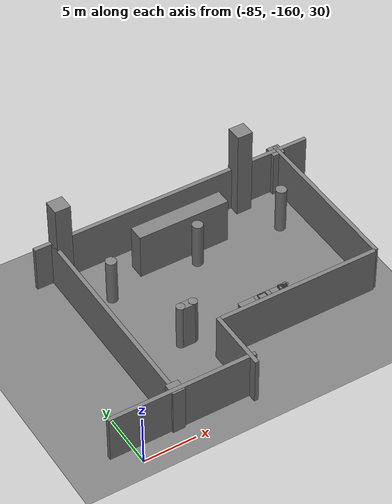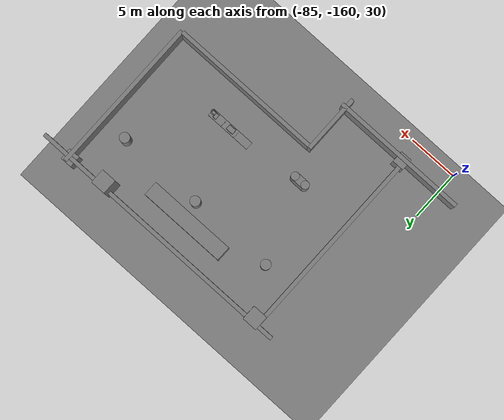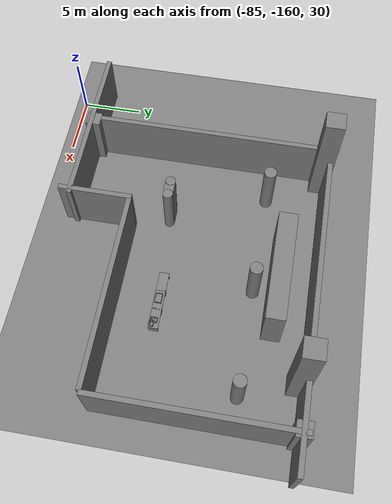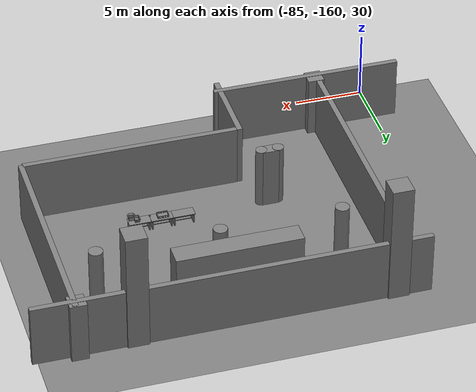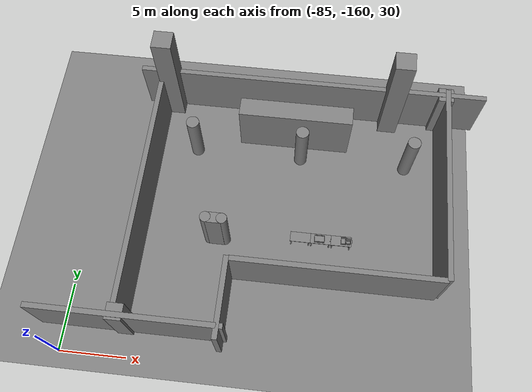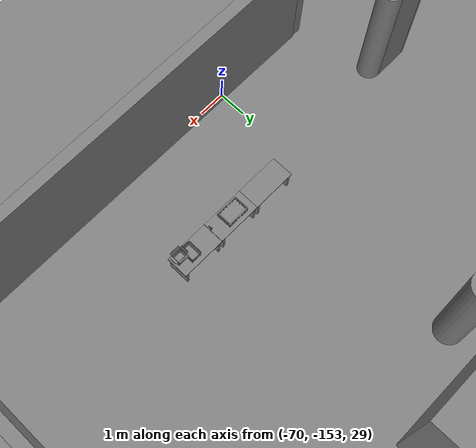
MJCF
<mujoco>
    <option gravity="0.000000000 0.000000000 -9.810000420" timestep="0.0049999999" integrator="implicitfast" density="1.225" viscosity="1.8000001e-05" noslip_iterations="10" iterations="100" sdf_iterations="50">
        <flag multiccd="disable"/>
    </option>
    <size memory="1000M"/>
    <compiler coordinate="local"/>
    <worldbody>
        <light cutoff="30" pos="0 1 1" dir="0 -1 -2"/>
        <light cutoff="30" pos="0 -1 1" dir="0 1 -2"/>
        <body pos="-64.866622925 -149.383972168 30.183746338" euler="89.999992371 89.999946594 0.000000000" name="openloong_gripper_2f85_fix_base_usda_bluebox_01">
            <geom contype="1" conaffinity="1" density="1000" type="box" material="" rgba="0.500000000 0.500000000 0.500000000 1.000000000" solimp="0.899999976 0.949999988 0.001000000" friction="1.000000000 0.005000000 0.000100000" solref="0.020000000 1.000000000" margin="0" condim="3" group="0" pos="0.276596069 0.187225342 0.000061035" quat="0.707107008 0.000077501 0.707106471 0.000077456" size="0.100000001 0.057999998 0.010000000" name="openloong_gripper_2f85_fix_base_usda_geom_5C652E85_CE31_4254_8153_CDDC23B52538"/>
            <geom contype="1" conaffinity="1" density="1000" type="box" material="" rgba="0.500000000 0.500000000 0.500000000 1.000000000" solimp="0.899999976 0.949999988 0.001000000" friction="1.000000000 0.005000000 0.000100000" solref="0.020000000 1.000000000" margin="0" condim="3" group="0" pos="0.000000000 0.002883911 0.000000000" quat="1.000000000 0.000000000 0.000000000 0.000000000" size="0.254000008 0.003000000 0.172000006" name="openloong_gripper_2f85_fix_base_usda_geom_BE4698C6_217A_4B31_961A_F6038C2E463C"/>
            <geom contype="1" conaffinity="1" density="1000" type="box" material="" rgba="0.500000000 0.500000000 0.500000000 1.000000000" solimp="0.899999976 0.949999988 0.001000000" friction="1.000000000 0.005000000 0.000100000" solref="0.020000000 1.000000000" margin="0" condim="3" group="0" pos="0.000015259 0.124874115 0.173477173" quat="0.999796450 0.020176515 -0.000000015 0.000000030" size="0.259999990 0.119999997 0.007000000" name="openloong_gripper_2f85_fix_base_usda_geom_3DE1EB52_7480_43A9_8122_45C7FF60D4D2"/>
            <geom contype="1" conaffinity="1" density="1000" type="box" material="" rgba="0.500000000 0.500000000 0.500000000 1.000000000" solimp="0.899999976 0.949999988 0.001000000" friction="1.000000000 0.005000000 0.000100000" solref="0.020000000 1.000000000" margin="0" condim="3" group="0" pos="0.000015259 0.124874115 -0.173477173" quat="0.999796450 -0.020176545 -0.000000015 0.000000000" size="0.259999990 0.119999997 0.007000000" name="openloong_gripper_2f85_fix_base_usda_geom_B749D62A_98BE_405D_90FA_56A04D81E532"/>
            <geom contype="1" conaffinity="1" density="1000" type="box" material="" rgba="0.500000000 0.500000000 0.500000000 1.000000000" solimp="0.899999976 0.949999988 0.001000000" friction="1.000000000 0.005000000 0.000100000" solref="0.020000000 1.000000000" margin="0" condim="3" group="0" pos="0.000015259 0.214012146 0.188980103" quat="0.999913096 0.013176724 0.000000015 0.000000000" size="0.259999990 0.029999999 0.012500000" name="openloong_gripper_2f85_fix_base_usda_geom_93952C2B_5636_4A97_A1C2_8215A9553249"/>
            <geom contype="1" conaffinity="1" density="1000" type="box" material="" rgba="0.500000000 0.500000000 0.500000000 1.000000000" solimp="0.899999976 0.949999988 0.001000000" friction="1.000000000 0.005000000 0.000100000" solref="0.020000000 1.000000000" margin="0" condim="3" group="0" pos="-0.258346558 0.125289917 0.001876831" quat="0.702796996 -0.020792052 0.710783184 0.020769238" size="0.189999998 0.119999997 0.009000000" name="openloong_gripper_2f85_fix_base_usda_geom_5C5822C6_D138_409F_A429_8EDDE6C99FB2"/>
            <geom contype="1" conaffinity="1" density="1000" type="box" material="" rgba="0.500000000 0.500000000 0.500000000 1.000000000" solimp="0.899999976 0.949999988 0.001000000" friction="1.000000000 0.005000000 0.000100000" solref="0.020000000 1.000000000" margin="0" condim="3" group="0" pos="0.000015259 0.214012146 -0.188980103" quat="0.999913096 -0.013176769 0.000000030 0.000000015" size="0.259999990 0.029999999 0.012500000" name="openloong_gripper_2f85_fix_base_usda_geom_BBDD1BBA_DAB0_4BC0_8EDC_AE3C9371BE6B"/>
            <geom contype="1" conaffinity="1" density="1000" type="box" material="" rgba="0.500000000 0.500000000 0.500000000 1.000000000" solimp="0.899999976 0.949999988 0.001000000" friction="1.000000000 0.005000000 0.000100000" solref="0.020000000 1.000000000" margin="0" condim="3" group="0" pos="-0.276596069 0.187225342 0.000061035" quat="0.707106650 0.000077441 0.707106709 0.000077456" size="0.100000001 0.057999998 0.010000000" name="openloong_gripper_2f85_fix_base_usda_geom_EE2F2F18_BA74_47F2_86FA_271558E28A8C"/>
            <geom contype="1" conaffinity="1" density="1000" type="box" material="" rgba="0.500000000 0.500000000 0.500000000 1.000000000" solimp="0.899999976 0.949999988 0.001000000" friction="1.000000000 0.005000000 0.000100000" solref="0.020000000 1.000000000" margin="0" condim="3" group="0" pos="0.258346558 0.125289917 0.001876831" quat="0.702851534 0.018856451 0.710823834 -0.019329429" size="0.189999998 0.119999997 0.009000000" name="openloong_gripper_2f85_fix_base_usda_geom_F365226F_E277_4C56_B8B9_5D840CB232FB"/>
            <freejoint name="openloong_gripper_2f85_fix_base_usda_bluebox_01_joint"/>
            <site size="0.005000000 0.005000000 0.005000000" rgba="0.500000000 0.500000000 0.500000000 1.000000000" pos="0.000000000 0.000000000 0.000000000" quat="0.999961913 0.008726534 0.000000000 0.000000000" group="0" type="sphere" name="openloong_gripper_2f85_fix_base_usda_bluebox_01site"/>
        </body>
        <body pos="-64.496299744 -149.491867065 30.235729218" euler="0.000000000 0.000000000 89.999946594" name="openloong_gripper_2f85_fix_base_usda_cardboardbox_01">
            <geom contype="1" conaffinity="1" density="1000" type="box" material="" rgba="0.500000000 0.500000000 0.500000000 1.000000000" solimp="0.899999976 0.949999988 0.001000000" friction="1.000000000 0.005000000 0.000100000" solref="0.020000000 1.000000000" margin="0" condim="3" group="0" pos="-0.003166199 -0.004086494 0.005052090" quat="1.000000000 0.000000000 0.000000000 0.000000000" size="0.142499998 0.177500010 0.005000000" name="openloong_gripper_2f85_fix_base_usda_geom_925EC49C_3446_452D_A654_3B28958FAD21"/>
            <geom contype="1" conaffinity="1" density="1000" type="box" material="" rgba="0.500000000 0.500000000 0.500000000 1.000000000" solimp="0.899999976 0.949999988 0.001000000" friction="1.000000000 0.005000000 0.000100000" solref="0.020000000 1.000000000" margin="0" condim="3" group="0" pos="-0.003166199 0.170316696 0.150570869" quat="1.000000000 0.000000000 0.000000000 0.000000000" size="0.142499998 0.005000000 0.149999991" name="openloong_gripper_2f85_fix_base_usda_geom_744F8B85_BFB2_40D0_9891_B9C2A27F3623"/>
            <geom contype="1" conaffinity="1" density="1000" type="box" material="" rgba="0.500000000 0.500000000 0.500000000 1.000000000" solimp="0.899999976 0.949999988 0.001000000" friction="1.000000000 0.005000000 0.000100000" solref="0.020000000 1.000000000" margin="0" condim="3" group="0" pos="-0.147399902 -0.005307198 0.150570869" quat="1.000000000 0.000000000 0.000000000 0.000000000" size="0.005000000 0.177500010 0.149999991" name="openloong_gripper_2f85_fix_base_usda_geom_F5794045_9E62_448A_A6E4_282C9B7944FA"/>
            <geom contype="1" conaffinity="1" density="1000" type="box" material="" rgba="0.500000000 0.500000000 0.500000000 1.000000000" solimp="0.899999976 0.949999988 0.001000000" friction="1.000000000 0.005000000 0.000100000" solref="0.020000000 1.000000000" margin="0" condim="3" group="0" pos="0.140275955 -0.005307198 0.150570869" quat="1.000000000 0.000000000 0.000000000 0.000000000" size="0.005000000 0.177500010 0.149999991" name="openloong_gripper_2f85_fix_base_usda_geom_A082079A_4092_4E5C_A59E_4378C05D1B58"/>
            <geom contype="1" conaffinity="1" density="1000" type="box" material="" rgba="0.500000000 0.500000000 0.500000000 1.000000000" solimp="0.899999976 0.949999988 0.001000000" friction="1.000000000 0.005000000 0.000100000" solref="0.020000000 1.000000000" margin="0" condim="3" group="0" pos="-0.003166199 -0.181550980 0.150570869" quat="1.000000000 0.000000000 0.000000000 0.000000000" size="0.142499998 0.005000000 0.149999991" name="openloong_gripper_2f85_fix_base_usda_geom_FC400E01_95F5_4EE7_B361_C840EE89694C"/>
            <freejoint name="openloong_gripper_2f85_fix_base_usda_cardboardbox_01_joint"/>
            <site size="0.005000000 0.005000000 0.005000000" rgba="0.500000000 0.500000000 0.500000000 1.000000000" pos="0.000000000 0.000000000 0.000000000" quat="0.999961913 0.008726535 0.000000000 0.000000000" group="0" type="sphere" name="openloong_gripper_2f85_fix_base_usda_site_EDCDE52B_0BE9_4F49_8E5E_A093D48B9047"/>
            <body pos="0.139160156 -0.004048347 0.301930904" euler="-179.999954224 49.383502960 179.999954224" name="openloong_gripper_2f85_fix_base_usda_A1_006">
                <geom contype="1" conaffinity="1" density="1000" type="box" material="" rgba="0.500000000 0.500000000 0.500000000 1.000000000" solimp="0.899999976 0.949999988 0.001000000" friction="1.000000000 0.005000000 0.000100000" solref="0.020000000 1.000000000" margin="0" condim="3" group="0" pos="-0.071587563 0.000009537 0.001745224" quat="0.999999881 0.000000000 0.000000000 0.000000000" size="0.071249999 0.179999992 0.002500000" name="openloong_gripper_2f85_fix_base_usda_geom_E98D13A1_5E08_411E_B249_C71C995E6A79"/>
                <joint armature="0" stiffness="0.07" damping="0.0099999998" axis="0.000000 1.000000 0.000000" type="hinge" name="openloong_gripper_2f85_fix_base_usda_A1_006"/>
            </body>
            <body pos="-0.145902634 -0.004086494 0.301938057" euler="-180.000000000 -60.000011444 -180.000000000" name="openloong_gripper_2f85_fix_base_usda_A2_006">
                <geom contype="1" conaffinity="1" density="1000" type="box" material="" rgba="0.500000000 0.500000000 0.500000000 1.000000000" solimp="0.899999976 0.949999988 0.001000000" friction="1.000000000 0.005000000 0.000100000" solref="0.020000000 1.000000000" margin="0" condim="3" group="0" pos="0.071268082 0.000009537 0.002717972" quat="0.000002921 0.000000000 -0.000000030 0.999999881" size="0.071249999 0.179999992 0.002500000" name="openloong_gripper_2f85_fix_base_usda_geom_F1F8D52C_7DE4_4FD6_ACC2_6F71AF6DEA9A"/>
                <joint armature="0" stiffness="0.07" damping="0.0099999998" axis="0.000000 1.000000 0.000000" type="hinge" name="openloong_gripper_2f85_fix_base_usda_A2_006"/>
            </body>
            <body pos="-0.003385544 0.175991058 0.301930904" euler="-125.858116150 -0.000004561 0.000002331" name="openloong_gripper_2f85_fix_base_usda_B2_006">
                <geom contype="1" conaffinity="1" density="1000" type="box" material="" rgba="0.500000000 0.500000000 0.500000000 1.000000000" solimp="0.899999976 0.949999988 0.001000000" friction="1.000000000 0.005000000 0.000100000" solref="0.020000000 1.000000000" margin="0" condim="3" group="0" pos="0.000009537 -0.070939064 -0.002470016" quat="0.999614120 0.027776197 -0.000000015 0.000000030" size="0.137500003 0.064999998 0.005000000" name="openloong_gripper_2f85_fix_base_usda_geom_CF4444EC_1253_49A6_84D5_0F9013C47E46"/>
                <joint armature="0" stiffness="0.07" damping="0.0099999998" axis="1.000000 0.000000 0.000000" type="hinge" name="openloong_gripper_2f85_fix_base_usda_B2_006"/>
            </body>
            <body pos="-0.003385544 -0.184140205 0.301938057" euler="147.805557251 0.000000000 0.000000000" name="openloong_gripper_2f85_fix_base_usda_B1_006">
                <geom contype="1" conaffinity="1" density="1000" type="box" material="" rgba="0.500000000 0.500000000 0.500000000 1.000000000" solimp="0.899999976 0.949999988 0.001000000" friction="1.000000000 0.005000000 0.000100000" solref="0.020000000 1.000000000" margin="0" condim="3" group="0" pos="-0.000028610 0.070202351 -0.002703667" quat="0.999614179 -0.027776167 0.000000000 0.000000000" size="0.137500003 0.064999998 0.005000000" name="openloong_gripper_2f85_fix_base_usda_geom_8E970CE1_72F9_4B53_8FA3_44C1F0399DF4"/>
                <joint armature="0" stiffness="0.07" damping="0.0099999998" axis="1.000000 0.000000 0.000000" type="hinge" name="openloong_gripper_2f85_fix_base_usda_B1_006"/>
            </body>
        </body>
        <body pos="-65.882858276 -149.481979370 30.229999542" euler="-64.487716675 0.000000000 0.000000000" name="openloong_gripper_2f85_fix_base_usda_Barcode">
            <geom contype="1" conaffinity="1" density="1000" type="box" material="" rgba="0.500000000 0.500000000 0.500000000 1.000000000" solimp="0.899999976 0.949999988 0.001000000" friction="1.000000000 0.005000000 0.000100000" solref="0.020000000 1.000000000" margin="0" condim="3" group="0" pos="0.000000000 0.013038635 0.001419067" quat="0.000000000 0.000000000 0.000000000 1.000000119" size="0.034000002 0.010000000 0.017999999" name="openloong_gripper_2f85_fix_base_usda_geom_0C802506_5B23_44C9_9C0F_C9530D7CB5AD"/>
            <geom contype="1" conaffinity="1" density="1000" type="box" material="" rgba="0.500000000 0.500000000 0.500000000 1.000000000" solimp="0.899999976 0.949999988 0.001000000" friction="1.000000000 0.005000000 0.000100000" solref="0.020000000 1.000000000" margin="0" condim="3" group="0" pos="0.000000000 -0.035301208 -0.007095337" quat="0.000000000 0.000000000 -0.043619365 0.999048233" size="0.028999999 0.010000000 0.020000000" name="openloong_gripper_2f85_fix_base_usda_geom_3EFA4A8F_9121_4BE8_94C4_1CC1F2621C2E"/>
            <geom contype="1" conaffinity="1" density="1000" type="box" material="" rgba="0.500000000 0.500000000 0.500000000 1.000000000" solimp="0.899999976 0.949999988 0.001000000" friction="1.000000000 0.005000000 0.000100000" solref="0.020000000 1.000000000" margin="0" condim="3" group="0" pos="0.000000000 -0.043411255 -0.011749268" quat="0.922262907 0.386563420 0.000000000 0.000000000" size="0.026000001 0.010000000 0.020000000" name="openloong_gripper_2f85_fix_base_usda_geom_632F741F_7696_41B0_924E_69F0597E7DDF"/>
            <geom contype="1" conaffinity="1" density="1000" type="box" material="" rgba="0.500000000 0.500000000 0.500000000 1.000000000" solimp="0.899999976 0.949999988 0.001000000" friction="1.000000000 0.005000000 0.000100000" solref="0.020000000 1.000000000" margin="0" condim="3" group="0" pos="0.000000000 -0.016967773 -0.031860352" quat="0.000000000 0.000000000 0.000000000 1.000000119" size="0.008000000 0.010000000 0.013000000" name="openloong_gripper_2f85_fix_base_usda_geom_AFF48DFC_EB32_4723_9BBA_8AFC077B59B5"/>
            <geom contype="1" conaffinity="1" density="1000" type="box" material="" rgba="0.500000000 0.500000000 0.500000000 1.000000000" solimp="0.899999976 0.949999988 0.001000000" friction="1.000000000 0.005000000 0.000100000" solref="0.020000000 1.000000000" margin="0" condim="3" group="0" pos="0.000000000 -0.001869202 0.000312805" quat="0.953716993 0.300705761 0.000000000 0.000000000" size="0.032000002 0.010000000 0.018999999" name="openloong_gripper_2f85_fix_base_usda_geom_78201378_555D_4BAD_8D39_FF7233D75F98"/>
            <geom contype="1" conaffinity="1" density="1000" type="box" material="" rgba="0.500000000 0.500000000 0.500000000 1.000000000" solimp="0.899999976 0.949999988 0.001000000" friction="1.000000000 0.005000000 0.000100000" solref="0.020000000 1.000000000" margin="0" condim="3" group="0" pos="0.000000000 -0.019531250 -0.003173828" quat="0.953716993 0.300705761 0.000000000 0.000000000" size="0.030999999 0.010000000 0.020000000" name="openloong_gripper_2f85_fix_base_usda_geom_88566E22_2A6A_4F72_8D91_45456C20FFF3"/>
            <geom contype="1" conaffinity="1" density="1000" type="box" material="" rgba="0.500000000 0.500000000 0.500000000 1.000000000" solimp="0.899999976 0.949999988 0.001000000" friction="1.000000000 0.005000000 0.000100000" solref="0.020000000 1.000000000" margin="0" condim="3" group="0" pos="0.000000000 -0.035301208 -0.007095337" quat="0.953716993 0.300705761 0.000000000 0.000000000" size="0.028999999 0.010000000 0.020000000" name="openloong_gripper_2f85_fix_base_usda_geom_9157E62F_13ED_4955_8244_64942BC7BDAA"/>
            <geom contype="1" conaffinity="1" density="1000" type="box" material="" rgba="0.500000000 0.500000000 0.500000000 1.000000000" solimp="0.899999976 0.949999988 0.001000000" friction="1.000000000 0.005000000 0.000100000" solref="0.020000000 1.000000000" margin="0" condim="3" group="0" pos="0.000000000 -0.042617798 -0.071121216" quat="0.000000000 0.000000000 0.000000000 1.000000119" size="0.013000000 0.021000000 0.059999999" name="openloong_gripper_2f85_fix_base_usda_geom_E86A24B3_4CC4_47E0_8E7C_37A008DCD059"/>
            <freejoint name="openloong_gripper_2f85_fix_base_usda_Barcode_joint"/>
            <site size="0.005000000 0.005000000 0.005000000" rgba="0.500000000 0.500000000 0.500000000 1.000000000" pos="0.000000000 0.000000000 0.000000000" quat="1.000000000 0.000000000 0.000000000 0.000000000" group="0" type="sphere" name="openloong_gripper_2f85_fix_base_usda_Barcode_site"/>
        </body>
        <body pos="-66.745018005 -149.392349243 30.184000015" euler="0.000000000 0.000000000 89.999946594" name="[22332184607084]_Basket_01">
            <geom contype="1" conaffinity="1" density="1000" type="box" material="" rgba="0.500000000 0.500000000 0.500000000 1.000000000" solimp="0.899999976 0.949999988 0.001000000" friction="1.000000000 0.005000000 0.000100000" solref="0.020000000 1.000000000" margin="0" condim="3" group="0" pos="-0.052425385 0.389207840 0.089787483" quat="0.707107008 0.000000000 0.000000000 0.707106411" size="0.014249999 0.014249999 0.059999999" name="[22332184607084]_geom_D6B78119_63BF_441B_A299_F480D8FB8E73"/>
            <geom contype="1" conaffinity="1" density="1000" type="box" material="" rgba="0.500000000 0.500000000 0.500000000 1.000000000" solimp="0.899999976 0.949999988 0.001000000" friction="1.000000000 0.005000000 0.000100000" solref="0.020000000 1.000000000" margin="0" condim="3" group="0" pos="0.264015198 -0.133043289 0.089787483" quat="0.707107008 0.000000000 0.000000000 0.707106411" size="0.014249999 0.014249999 0.059999999" name="[22332184607084]_geom_7019BA1F_F9AC_449D_8722_4794B1CB86E3"/>
            <geom contype="1" conaffinity="1" density="1000" type="box" material="" rgba="0.500000000 0.500000000 0.500000000 1.000000000" solimp="0.899999976 0.949999988 0.001000000" friction="1.000000000 0.005000000 0.000100000" solref="0.020000000 1.000000000" margin="0" condim="3" group="0" pos="-0.264015198 -0.265548706 0.089793205" quat="0.707107008 0.000000000 0.000000000 0.707106411" size="0.014249999 0.014249999 0.059999999" name="[22332184607084]_geom_14E8C485_C2C1_4A87_8CF8_C7591C60CEEF"/>
            <geom contype="1" conaffinity="1" density="1000" type="box" material="" rgba="0.500000000 0.500000000 0.500000000 1.000000000" solimp="0.899999976 0.949999988 0.001000000" friction="1.000000000 0.005000000 0.000100000" solref="0.020000000 1.000000000" margin="0" condim="3" group="0" pos="-0.160263062 -0.389322281 0.089793205" quat="0.707107008 0.000000000 0.000000000 0.707106411" size="0.014249999 0.014249999 0.059999999" name="[22332184607084]_geom_F3B66D7C_E847_4C88_B7C3_B44EFB4DAD82"/>
            <geom contype="1" conaffinity="1" density="1000" type="box" material="" rgba="0.500000000 0.500000000 0.500000000 1.000000000" solimp="0.899999976 0.949999988 0.001000000" friction="1.000000000 0.005000000 0.000100000" solref="0.020000000 1.000000000" margin="0" condim="3" group="0" pos="0.162265778 -0.389322281 0.089787483" quat="0.707107008 0.000000000 0.000000000 0.707106411" size="0.014249999 0.014249999 0.059999999" name="[22332184607084]_geom_6647828C_B62B_4603_94D9_834CC89A8605"/>
            <geom contype="1" conaffinity="1" density="1000" type="box" material="" rgba="0.500000000 0.500000000 0.500000000 1.000000000" solimp="0.899999976 0.949999988 0.001000000" friction="1.000000000 0.005000000 0.000100000" solref="0.020000000 1.000000000" margin="0" condim="3" group="0" pos="0.264015198 0.389207840 0.089787483" quat="0.707107008 0.000000000 0.000000000 0.707106411" size="0.014249999 0.014249999 0.059999999" name="[22332184607084]_geom_CEF27B8C_CF29_47A3_AF01_F86DB294A2F9"/>
            <geom contype="1" conaffinity="1" density="1000" type="box" material="" rgba="0.500000000 0.500000000 0.500000000 1.000000000" solimp="0.899999976 0.949999988 0.001000000" friction="1.000000000 0.005000000 0.000100000" solref="0.020000000 1.000000000" margin="0" condim="3" group="0" pos="-0.264015198 -0.133043289 0.089793205" quat="0.707107008 0.000000000 0.000000000 0.707106411" size="0.014249999 0.014249999 0.059999999" name="[22332184607084]_geom_BFED3350_7285_426C_B605_6B92224B7208"/>
            <geom contype="1" conaffinity="1" density="1000" type="box" material="" rgba="0.500000000 0.500000000 0.500000000 1.000000000" solimp="0.899999976 0.949999988 0.001000000" friction="1.000000000 0.005000000 0.000100000" solref="0.020000000 1.000000000" margin="0" condim="3" group="0" pos="-0.264026642 0.269256592 0.089793205" quat="0.707107008 0.000000000 0.000000000 0.707106411" size="0.014249999 0.014249999 0.059999999" name="[22332184607084]_geom_3EBC197E_EED9_49FB_B21D_E929A956F052"/>
            <geom contype="1" conaffinity="1" density="1000" type="box" material="" rgba="0.500000000 0.500000000 0.500000000 1.000000000" solimp="0.899999976 0.949999988 0.001000000" friction="1.000000000 0.005000000 0.000100000" solref="0.020000000 1.000000000" margin="0" condim="3" group="0" pos="0.054462433 0.389207840 0.089787483" quat="0.707107008 0.000000000 0.000000000 0.707106411" size="0.014249999 0.014249999 0.059999999" name="[22332184607084]_geom_B8150F7F_5E40_4FC3_950B_9D68EBF2FFDC"/>
            <geom contype="1" conaffinity="1" density="1000" type="box" material="" rgba="0.500000000 0.500000000 0.500000000 1.000000000" solimp="0.899999976 0.949999988 0.001000000" friction="1.000000000 0.005000000 0.000100000" solref="0.020000000 1.000000000" margin="0" condim="3" group="0" pos="0.054462433 -0.389322281 0.089787483" quat="0.707107008 0.000000000 0.000000000 0.707106411" size="0.014249999 0.014249999 0.059999999" name="[22332184607084]_geom_BE1BC5F9_FFD1_48AE_AD7A_7ACB94BAF576"/>
            <geom contype="1" conaffinity="1" density="1000" type="box" material="" rgba="0.500000000 0.500000000 0.500000000 1.000000000" solimp="0.899999976 0.949999988 0.001000000" friction="1.000000000 0.005000000 0.000100000" solref="0.020000000 1.000000000" margin="0" condim="3" group="0" pos="0.264015198 0.269256592 0.089793205" quat="0.707107008 0.000000000 0.000000000 0.707106411" size="0.014249999 0.014249999 0.059999999" name="[22332184607084]_geom_743DA80A_C9EE_4441_8162_7387C229E519"/>
            <geom contype="1" conaffinity="1" density="1000" type="box" material="" rgba="0.500000000 0.500000000 0.500000000 1.000000000" solimp="0.899999976 0.949999988 0.001000000" friction="1.000000000 0.005000000 0.000100000" solref="0.020000000 1.000000000" margin="0" condim="3" group="0" pos="0.264015198 -0.389322281 0.089787483" quat="0.707107008 0.000000000 0.000000000 0.707106411" size="0.014249999 0.014249999 0.059999999" name="[22332184607084]_geom_DECF3063_F491_4A79_A205_CD44274B6FFB"/>
            <geom contype="1" conaffinity="1" density="1000" type="box" material="" rgba="0.500000000 0.500000000 0.500000000 1.000000000" solimp="0.899999976 0.949999988 0.001000000" friction="1.000000000 0.005000000 0.000100000" solref="0.020000000 1.000000000" margin="0" condim="3" group="0" pos="0.000000000 0.000000000 0.015998840" quat="0.707107008 0.000000000 0.000000000 0.707106411" size="0.403499991 0.279000014 0.015750000" name="[22332184607084]_geom_1447F760_C2F5_4432_A1CA_4B9BA95E8F8D"/>
            <geom contype="1" conaffinity="1" density="1000" type="box" material="" rgba="0.500000000 0.500000000 0.500000000 1.000000000" solimp="0.899999976 0.949999988 0.001000000" friction="1.000000000 0.005000000 0.000100000" solref="0.020000000 1.000000000" margin="0" condim="3" group="0" pos="0.000000000 -0.389476776 0.163619041" quat="0.707107008 0.000000000 0.000000000 0.707106411" size="0.015000000 0.277500004 0.015750000" name="[22332184607084]_geom_F1FB6258_0C66_48FF_9D20_D187EB9DE82E"/>
            <geom contype="1" conaffinity="1" density="1000" type="box" material="" rgba="0.500000000 0.500000000 0.500000000 1.000000000" solimp="0.899999976 0.949999988 0.001000000" friction="1.000000000 0.005000000 0.000100000" solref="0.020000000 1.000000000" margin="0" condim="3" group="0" pos="0.162265778 0.389207840 0.089787483" quat="0.707107008 0.000000000 0.000000000 0.707106411" size="0.014249999 0.014249999 0.059999999" name="[22332184607084]_geom_EFBBC014_81FD_45F9_9913_486EE1A9257A"/>
            <geom contype="1" conaffinity="1" density="1000" type="box" material="" rgba="0.500000000 0.500000000 0.500000000 1.000000000" solimp="0.899999976 0.949999988 0.001000000" friction="1.000000000 0.005000000 0.000100000" solref="0.020000000 1.000000000" margin="0" condim="3" group="0" pos="0.000000000 0.389471054 0.163619041" quat="0.707107008 0.000000000 0.000000000 0.707106411" size="0.015000000 0.277500004 0.015750000" name="[22332184607084]_geom_F92EC856_A936_4877_B55E_52E19DF1857C"/>
            <geom contype="1" conaffinity="1" density="1000" type="box" material="" rgba="0.500000000 0.500000000 0.500000000 1.000000000" solimp="0.899999976 0.949999988 0.001000000" friction="1.000000000 0.005000000 0.000100000" solref="0.020000000 1.000000000" margin="0" condim="3" group="0" pos="-0.263511658 0.000000000 0.163619041" quat="0.707107008 0.000000000 0.000000000 0.707106411" size="0.403499991 0.015000000 0.015750000" name="[22332184607084]_geom_C8AF80BC_4BB3_489D_9EB3_A3B9ECBC9F68"/>
            <geom contype="1" conaffinity="1" density="1000" type="box" material="" rgba="0.500000000 0.500000000 0.500000000 1.000000000" solimp="0.899999976 0.949999988 0.001000000" friction="1.000000000 0.005000000 0.000100000" solref="0.020000000 1.000000000" margin="0" condim="3" group="0" pos="-0.264015198 0.141334534 0.089793205" quat="0.707107008 0.000000000 0.000000000 0.707106411" size="0.014249999 0.014249999 0.059999999" name="[22332184607084]_geom_E67C58E6_D23A_42A4_A71A_8A0EE667874C"/>
            <geom contype="1" conaffinity="1" density="1000" type="box" material="" rgba="0.500000000 0.500000000 0.500000000 1.000000000" solimp="0.899999976 0.949999988 0.001000000" friction="1.000000000 0.005000000 0.000100000" solref="0.020000000 1.000000000" margin="0" condim="3" group="0" pos="0.264015198 -0.265548706 0.089787483" quat="0.707107008 0.000000000 0.000000000 0.707106411" size="0.014249999 0.014249999 0.059999999" name="[22332184607084]_geom_4A65506B_3468_44BD_9AA8_53D8CDF1E61C"/>
            <geom contype="1" conaffinity="1" density="1000" type="box" material="" rgba="0.500000000 0.500000000 0.500000000 1.000000000" solimp="0.899999976 0.949999988 0.001000000" friction="1.000000000 0.005000000 0.000100000" solref="0.020000000 1.000000000" margin="0" condim="3" group="0" pos="-0.160263062 0.389207840 0.089787483" quat="0.707107008 0.000000000 0.000000000 0.707106411" size="0.014249999 0.014249999 0.059999999" name="[22332184607084]_geom_C8F91B2E_5296_4585_8BB8_CC740A3236C7"/>
            <geom contype="1" conaffinity="1" density="1000" type="box" material="" rgba="0.500000000 0.500000000 0.500000000 1.000000000" solimp="0.899999976 0.949999988 0.001000000" friction="1.000000000 0.005000000 0.000100000" solref="0.020000000 1.000000000" margin="0" condim="3" group="0" pos="-0.052425385 -0.389322281 0.089787483" quat="0.707107008 0.000000000 0.000000000 0.707106411" size="0.014249999 0.014249999 0.059999999" name="[22332184607084]_geom_1EEE0916_79AF_446E_942C_B615789D38D6"/>
            <geom contype="1" conaffinity="1" density="1000" type="box" material="" rgba="0.500000000 0.500000000 0.500000000 1.000000000" solimp="0.899999976 0.949999988 0.001000000" friction="1.000000000 0.005000000 0.000100000" solref="0.020000000 1.000000000" margin="0" condim="3" group="0" pos="-0.264026642 -0.389322281 0.089793205" quat="0.707107008 0.000000000 0.000000000 0.707106411" size="0.014249999 0.014249999 0.059999999" name="[22332184607084]_geom_80AA6779_A256_41C3_8F58_C4DCC36D2660"/>
            <geom contype="1" conaffinity="1" density="1000" type="box" material="" rgba="0.500000000 0.500000000 0.500000000 1.000000000" solimp="0.899999976 0.949999988 0.001000000" friction="1.000000000 0.005000000 0.000100000" solref="0.020000000 1.000000000" margin="0" condim="3" group="0" pos="0.264015198 0.141334534 0.089787483" quat="0.707107008 0.000000000 0.000000000 0.707106411" size="0.014249999 0.014249999 0.059999999" name="[22332184607084]_geom_6E651FB8_0731_4977_99CB_6AC4169725C0"/>
            <geom contype="1" conaffinity="1" density="1000" type="box" material="" rgba="0.500000000 0.500000000 0.500000000 1.000000000" solimp="0.899999976 0.949999988 0.001000000" friction="1.000000000 0.005000000 0.000100000" solref="0.020000000 1.000000000" margin="0" condim="3" group="0" pos="-0.264015198 0.389207840 0.089793205" quat="0.707107008 0.000000000 0.000000000 0.707106411" size="0.014249999 0.014249999 0.059999999" name="[22332184607084]_geom_61936F23_AF9A_4C23_ADD5_4B0BAED771B7"/>
            <geom contype="1" conaffinity="1" density="1000" type="box" material="" rgba="0.500000000 0.500000000 0.500000000 1.000000000" solimp="0.899999976 0.949999988 0.001000000" friction="1.000000000 0.005000000 0.000100000" solref="0.020000000 1.000000000" margin="0" condim="3" group="0" pos="0.264015198 0.004480362 0.089787483" quat="0.707107008 0.000000000 0.000000000 0.707106411" size="0.014249999 0.014249999 0.059999999" name="[22332184607084]_geom_3BAB2A1D_82E8_4709_9EE9_15719ECCA474"/>
            <geom contype="1" conaffinity="1" density="1000" type="box" material="" rgba="0.500000000 0.500000000 0.500000000 1.000000000" solimp="0.899999976 0.949999988 0.001000000" friction="1.000000000 0.005000000 0.000100000" solref="0.020000000 1.000000000" margin="0" condim="3" group="0" pos="0.263694763 -0.000011444 0.163619041" quat="0.707107008 0.000000000 0.000000000 0.707106411" size="0.403499991 0.015000000 0.015750000" name="[22332184607084]_geom_C838E8AF_7C7B_4579_AF97_19A13A209FE3"/>
            <geom contype="1" conaffinity="1" density="1000" type="box" material="" rgba="0.500000000 0.500000000 0.500000000 1.000000000" solimp="0.899999976 0.949999988 0.001000000" friction="1.000000000 0.005000000 0.000100000" solref="0.020000000 1.000000000" margin="0" condim="3" group="0" pos="-0.264015198 0.004480362 0.089793205" quat="0.707107008 0.000000000 0.000000000 0.707106411" size="0.014249999 0.014249999 0.059999999" name="[22332184607084]_geom_D4AE7DF3_FE12_4B12_A2CB_41E6F662D908"/>
            <freejoint name="[22332184607084]_joint_70FCB9F4_9D2F_4D1A_BE32_655C77B8F3E9"/>
        </body>
        <body pos="0.000000000 0.000000000 0.000000000" euler="0.000000000 0.000000000 0.000000000" name="Static Objects_Static Objects">
            <geom contype="1" conaffinity="1" density="1000" type="box" material="" rgba="0.500000000 0.500000000 0.500000000 1.000000000" solimp="0.899999976 0.949999988 0.001000000" friction="1.000000000 0.005000000 0.000100000" solref="0.020000000 1.000000000" margin="0" condim="3" group="0" pos="-67.544113159 -149.365814209 29.727830887" quat="0.500000417 0.499999970 0.499999553 0.499999970" size="0.381000012 0.319999993 0.041000001" name="Static Objects_geom_1D20D5F8_B9D3_4F63_A1FD_531AF323FAA3"/>
            <geom contype="1" conaffinity="1" density="1000" type="box" material="" rgba="0.500000000 0.500000000 0.500000000 1.000000000" solimp="0.899999976 0.949999988 0.001000000" friction="1.000000000 0.005000000 0.000100000" solref="0.020000000 1.000000000" margin="0" condim="3" group="0" pos="-68.239501953 -149.365814209 30.086868286" quat="0.500000417 0.499999970 0.499999553 0.499999970" size="0.370999992 0.039500002 0.745000005" name="Static Objects_geom_64032F39_533C_4F7B_9EF1_A0BB9A416EDF"/>
            <geom contype="1" conaffinity="1" density="1000" type="box" material="" rgba="0.500000000 0.500000000 0.500000000 1.000000000" solimp="0.899999976 0.949999988 0.001000000" friction="1.000000000 0.005000000 0.000100000" solref="0.020000000 1.000000000" margin="0" condim="3" group="0" pos="-68.239501953 -149.365814209 30.147235870" quat="0.500000417 0.499999970 0.499999553 0.499999970" size="0.400000006 0.022000000 0.800000012" name="Static Objects_geom_6CAAD2D6_B8ED_4024_9AB9_D2617F9D8A85"/>
            <geom contype="1" conaffinity="1" density="1000" type="box" material="" rgba="0.500000000 0.500000000 0.500000000 1.000000000" solimp="0.899999976 0.949999988 0.001000000" friction="1.000000000 0.005000000 0.000100000" solref="0.020000000 1.000000000" margin="0" condim="3" group="0" pos="-68.934890747 -149.365814209 29.727830887" quat="0.500000417 0.499999970 0.499999553 0.499999970" size="0.381000012 0.319999993 0.041000001" name="Static Objects_geom_C96F2D35_3D60_4B3E_98CC_5C96D467C262"/>
            <geom contype="1" conaffinity="1" density="1000" type="box" material="" rgba="0.500000000 0.500000000 0.500000000 1.000000000" solimp="0.899999976 0.949999988 0.001000000" friction="1.000000000 0.005000000 0.000100000" solref="0.020000000 1.000000000" margin="0" condim="3" group="0" pos="-68.239501953 -149.365814209 29.561563492" quat="0.500000417 0.499999970 0.499999553 0.499999970" size="0.020000000 0.022000000 0.660000026" name="Static Objects_geom_CC2EC09D_D417_44A5_8C14_3AD4FCB05A3F"/>
            <geom contype="1" conaffinity="1" density="1000" type="box" material="" rgba="0.500000000 0.500000000 0.500000000 1.000000000" solimp="0.899999976 0.949999988 0.001000000" friction="1.000000000 0.005000000 0.000100000" solref="0.020000000 1.000000000" margin="0" condim="3" group="0" pos="-65.945671082 -149.365814209 29.727830887" quat="0.500000417 0.499999970 0.499999553 0.499999970" size="0.381000012 0.319999993 0.041000001" name="Static Objects_geom_1A00D789_58D4_42EB_92F6_259A1A433269"/>
            <geom contype="1" conaffinity="1" density="1000" type="box" material="" rgba="0.500000000 0.500000000 0.500000000 1.000000000" solimp="0.899999976 0.949999988 0.001000000" friction="1.000000000 0.005000000 0.000100000" solref="0.020000000 1.000000000" margin="0" condim="3" group="0" pos="-66.641059875 -149.365814209 30.086868286" quat="0.500000417 0.499999970 0.499999553 0.499999970" size="0.370999992 0.039500002 0.745000005" name="Static Objects_geom_ABA842EB_9AC6_4129_9867_31B8E96C54FB"/>
            <geom contype="1" conaffinity="1" density="1000" type="box" material="" rgba="0.500000000 0.500000000 0.500000000 1.000000000" solimp="0.899999976 0.949999988 0.001000000" friction="1.000000000 0.005000000 0.000100000" solref="0.020000000 1.000000000" margin="0" condim="3" group="0" pos="-66.641059875 -149.365814209 30.147235870" quat="0.500000417 0.499999970 0.499999553 0.499999970" size="0.400000006 0.022000000 0.800000012" name="Static Objects_geom_A092A9CA_1A91_4724_9E95_E4B676E7F10E"/>
            <geom contype="1" conaffinity="1" density="1000" type="box" material="" rgba="0.500000000 0.500000000 0.500000000 1.000000000" solimp="0.899999976 0.949999988 0.001000000" friction="1.000000000 0.005000000 0.000100000" solref="0.020000000 1.000000000" margin="0" condim="3" group="0" pos="-67.336448669 -149.365814209 29.727830887" quat="0.500000417 0.499999970 0.499999553 0.499999970" size="0.381000012 0.319999993 0.041000001" name="Static Objects_geom_619F8E2F_6412_4F94_ABF9_1D12F3138457"/>
            <geom contype="1" conaffinity="1" density="1000" type="box" material="" rgba="0.500000000 0.500000000 0.500000000 1.000000000" solimp="0.899999976 0.949999988 0.001000000" friction="1.000000000 0.005000000 0.000100000" solref="0.020000000 1.000000000" margin="0" condim="3" group="0" pos="-66.641059875 -149.365814209 29.561563492" quat="0.500000417 0.499999970 0.499999553 0.499999970" size="0.020000000 0.022000000 0.660000026" name="Static Objects_geom_B7DFA6E5_798D_4BFA_A479_C4189B0C1444"/>
            <geom contype="1" conaffinity="1" density="1000" type="box" material="" rgba="0.500000000 0.500000000 0.500000000 1.000000000" solimp="0.899999976 0.949999988 0.001000000" friction="1.000000000 0.005000000 0.000100000" solref="0.020000000 1.000000000" margin="0" condim="3" group="0" pos="-64.338577271 -149.365814209 29.727830887" quat="0.500000417 0.499999970 0.499999553 0.499999970" size="0.381000012 0.319999993 0.041000001" name="Static Objects_geom_A396BE2F_16C2_4F3C_8B93_70912204D89E"/>
            <geom contype="1" conaffinity="1" density="1000" type="box" material="" rgba="0.500000000 0.500000000 0.500000000 1.000000000" solimp="0.899999976 0.949999988 0.001000000" friction="1.000000000 0.005000000 0.000100000" solref="0.020000000 1.000000000" margin="0" condim="3" group="0" pos="-65.033966064 -149.365814209 30.086868286" quat="0.500000417 0.499999970 0.499999553 0.499999970" size="0.370999992 0.039500002 0.745000005" name="Static Objects_geom_57FEAED2_377B_459C_85FF_6674DADC0AE4"/>
            <geom contype="1" conaffinity="1" density="1000" type="box" material="" rgba="0.500000000 0.500000000 0.500000000 1.000000000" solimp="0.899999976 0.949999988 0.001000000" friction="1.000000000 0.005000000 0.000100000" solref="0.020000000 1.000000000" margin="0" condim="3" group="0" pos="-65.033966064 -149.365814209 30.147235870" quat="0.500000417 0.499999970 0.499999553 0.499999970" size="0.400000006 0.022000000 0.800000012" name="Static Objects_geom_30B872D4_AAA1_480B_80F2_E884C86FD124"/>
            <geom contype="1" conaffinity="1" density="1000" type="box" material="" rgba="0.500000000 0.500000000 0.500000000 1.000000000" solimp="0.899999976 0.949999988 0.001000000" friction="1.000000000 0.005000000 0.000100000" solref="0.020000000 1.000000000" margin="0" condim="3" group="0" pos="-65.729354858 -149.365814209 29.727830887" quat="0.500000417 0.499999970 0.499999553 0.499999970" size="0.381000012 0.319999993 0.041000001" name="Static Objects_geom_758C3E68_894A_433B_B2A3_CFD112FEB69E"/>
            <geom contype="1" conaffinity="1" density="1000" type="box" material="" rgba="0.500000000 0.500000000 0.500000000 1.000000000" solimp="0.899999976 0.949999988 0.001000000" friction="1.000000000 0.005000000 0.000100000" solref="0.020000000 1.000000000" margin="0" condim="3" group="0" pos="-65.033966064 -149.365814209 29.561563492" quat="0.500000417 0.499999970 0.499999553 0.499999970" size="0.020000000 0.022000000 0.660000026" name="Static Objects_geom_A1111FDE_5FB6_4AEC_8970_13605DE58E1B"/>
            <geom contype="1" conaffinity="1" density="1000" type="box" material="" rgba="0.500000000 0.500000000 0.500000000 1.000000000" solimp="0.899999976 0.949999988 0.001000000" friction="1.000000000 0.005000000 0.000100000" solref="0.020000000 1.000000000" margin="0" condim="3" group="0" pos="-61.754566193 -137.853729248 33.906845093" quat="0.707107067 0.000000000 0.000000000 0.707106471" size="0.759999990 0.759999990 4.500000000" name="Static Objects_geom_A004D81E_B25E_4F5D_919B_CF0BCDCCFE29"/>
            <geom contype="1" conaffinity="1" density="1000" type="box" material="" rgba="0.500000000 0.500000000 0.500000000 1.000000000" solimp="0.899999976 0.949999988 0.001000000" friction="1.000000000 0.005000000 0.000100000" solref="0.020000000 1.000000000" margin="0" condim="3" group="0" pos="-57.511135101 -144.927108765 31.707921982" quat="1.000000000 0.000000000 0.000000000 0.000000000" size="0.200000003 8.000000000 2.299999952" name="Static Objects_geom_47315D21_8048_4E04_8BFC_4BA0234AA9A3"/>
            <geom contype="1" conaffinity="1" density="1000" type="box" material="" rgba="0.500000000 0.500000000 0.500000000 1.000000000" solimp="0.899999976 0.949999988 0.001000000" friction="1.000000000 0.005000000 0.000100000" solref="0.020000000 1.000000000" margin="0" condim="3" group="0" pos="-80.517646790 -157.574050903 31.688196182" quat="0.707107067 0.000000000 0.000000000 0.707106471" size="0.600000024 0.600000024 2.299999952" name="Static Objects_geom_550A4D9C_7038_4355_BC36_87E476138100"/>
            <geom contype="1" conaffinity="1" density="1000" type="box" material="" rgba="0.500000000 0.500000000 0.500000000 1.000000000" solimp="0.899999976 0.949999988 0.001000000" friction="1.000000000 0.005000000 0.000100000" solref="0.020000000 1.000000000" margin="0" condim="3" group="0" pos="-80.711044312 -147.414932251 31.666158676" quat="1.000000000 0.000000000 0.000000000 0.000000000" size="0.200000003 10.000000000 2.299999952" name="Static Objects_geom_A4FA54BE_1C55_4BA3_B097_0BD51BE157E7"/>
            <geom contype="1" conaffinity="1" density="1000" type="box" material="" rgba="0.500000000 0.500000000 0.500000000 1.000000000" solimp="0.899999976 0.949999988 0.001000000" friction="1.000000000 0.005000000 0.000100000" solref="0.020000000 1.000000000" margin="0" condim="3" group="0" pos="-57.687217712 -137.434692383 31.688196182" quat="0.707107067 0.000000000 0.000000000 0.707106471" size="0.600000024 0.600000024 2.299999952" name="Static Objects_geom_C3D72884_24AF_4CC9_AF05_8D1865CD5687"/>
            <geom contype="1" conaffinity="1" density="1000" type="box" material="" rgba="0.500000000 0.500000000 0.500000000 1.000000000" solimp="0.899999976 0.949999988 0.001000000" friction="1.000000000 0.005000000 0.000100000" solref="0.020000000 1.000000000" margin="0" condim="3" group="0" pos="-69.537033081 -140.263229370 31.714921951" quat="0.707107067 0.000000000 0.000000000 0.707106471" size="0.759999990 4.500000000 2.299999952" name="Static Objects_geom_66E10B6A_8BF3_4A29_B98C_AE6373BF3F1B"/>
            <geom contype="1" conaffinity="1" density="1000" type="box" material="" rgba="0.500000000 0.500000000 0.500000000 1.000000000" solimp="0.899999976 0.949999988 0.001000000" friction="1.000000000 0.005000000 0.000100000" solref="0.020000000 1.000000000" margin="0" condim="3" group="0" pos="-80.073638916 -137.853713989 33.906845093" quat="0.707107067 0.000000000 0.000000000 0.707106471" size="0.759999990 0.759999990 4.500000000" name="Static Objects_geom_AB93E777_C242_4132_B9B4_FE3DC51BB79E"/>
            <geom contype="1" conaffinity="1" density="1000" type="box" material="" rgba="0.500000000 0.500000000 0.500000000 1.000000000" solimp="0.899999976 0.949999988 0.001000000" friction="1.000000000 0.005000000 0.000100000" solref="0.020000000 1.000000000" margin="0" condim="3" group="0" pos="-73.406707764 -155.734664917 31.707921982" quat="1.000000000 0.000000000 0.000000000 0.000000000" size="0.200000003 3.000000000 2.299999952" name="Static Objects_geom_7186190A_1F6E_4E81_80B9_56AEE53279E3"/>
            <geom contype="1" conaffinity="1" density="1000" type="box" material="" rgba="0.500000000 0.500000000 0.500000000 1.000000000" solimp="0.899999976 0.949999988 0.001000000" friction="1.000000000 0.005000000 0.000100000" solref="0.020000000 1.000000000" margin="0" condim="3" group="0" pos="-68.497543335 -137.448257446 31.707921982" quat="0.707107067 0.000000000 0.000000000 0.707106471" size="0.200000003 14.000000000 2.299999952" name="Static Objects_geom_C9432BF4_ECE5_4423_B15B_E5641FD7CBA6"/>
            <geom contype="1" conaffinity="1" density="1000" type="cylinder" material="" rgba="0.500000000 0.500000000 0.500000000 1.000000000" solimp="0.899999976 0.949999988 0.001000000" friction="1.000000000 0.005000000 0.000100000" solref="0.020000000 1.000000000" margin="0" condim="3" group="0" pos="-68.868522644 -142.134506226 31.711090088" quat="0.707107067 0.000000000 0.000000000 0.707106471" size="0.509999990 2.299999952 1.000000000" name="Static Objects_geom_3A268C64_8961_4EED_804F_0FF8DBEBC1F3"/>
            <geom contype="1" conaffinity="1" density="1000" type="plane" material="" rgba="0.500000000 0.500000000 0.500000000 1.000000000" solimp="0.899999976 0.949999988 0.001000000" friction="1.000000000 0.005000000 0.000100000" solref="0.020000000 1.000000000" margin="0" condim="3" group="0" pos="-72.873703003 -147.131927490 29.409669876" quat="1.000000000 0.000000000 0.000000000 0.000000000" size="18.000000000 14.000000000 1.000000000" name="Static Objects_geom_A91962DD_8584_483F_96E7_7B8C5D645563"/>
            <geom contype="1" conaffinity="1" density="1000" type="box" material="" rgba="0.500000000 0.500000000 0.500000000 1.000000000" solimp="0.899999976 0.949999988 0.001000000" friction="1.000000000 0.005000000 0.000100000" solref="0.020000000 1.000000000" margin="0" condim="3" group="0" pos="-79.943580627 -157.782272339 31.707921982" quat="0.707107067 0.000000000 0.000000000 0.707106471" size="0.200000003 7.000000000 2.299999952" name="Static Objects_geom_223AF588_2C87_435F_8865_F1765358594A"/>
            <geom contype="1" conaffinity="1" density="1000" type="box" material="" rgba="0.500000000 0.500000000 0.500000000 1.000000000" solimp="0.899999976 0.949999988 0.001000000" friction="1.000000000 0.005000000 0.000100000" solref="0.020000000 1.000000000" margin="0" condim="3" group="0" pos="-65.421028137 -152.903442383 31.707921982" quat="0.707107067 0.000000000 0.000000000 0.707106471" size="0.200000003 7.800000191 2.299999952" name="Static Objects_geom_B7BD7EE2_2295_4325_B3CD_2B2ADC29F21C"/>
            <geom contype="1" conaffinity="1" density="1000" type="box" material="" rgba="0.500000000 0.500000000 0.500000000 1.000000000" solimp="0.899999976 0.949999988 0.001000000" friction="1.000000000 0.005000000 0.000100000" solref="0.020000000 1.000000000" margin="0" condim="3" group="0" pos="-74.776908875 -149.964416504 31.688196182" quat="1.000000000 0.000000000 0.000000000 0.000000000" size="0.600000024 0.409999996 2.299999952" name="Static Objects_geom_F3883FC3_24DD_4D20_910A_7AB965CB01F1"/>
            <geom contype="1" conaffinity="1" density="1000" type="cylinder" material="" rgba="0.500000000 0.500000000 0.500000000 1.000000000" solimp="0.899999976 0.949999988 0.001000000" friction="1.000000000 0.005000000 0.000100000" solref="0.020000000 1.000000000" margin="0" condim="3" group="0" pos="-60.161884308 -142.134506226 31.711090088" quat="0.707107067 0.000000000 0.000000000 0.707106471" size="0.509999990 2.299999952 1.000000000" name="Static Objects_geom_D32048F0_95B8_4BF3_BBAF_5A99AF57E3C3"/>
            <geom contype="1" conaffinity="1" density="1000" type="cylinder" material="" rgba="0.500000000 0.500000000 0.500000000 1.000000000" solimp="0.899999976 0.949999988 0.001000000" friction="1.000000000 0.005000000 0.000100000" solref="0.020000000 1.000000000" margin="0" condim="3" group="0" pos="-75.382453918 -149.963455200 31.711090088" quat="0.707107067 0.000000000 0.000000000 0.707106471" size="0.409999996 2.299999952 1.000000000" name="Static Objects_geom_773A0E6C_F9B6_435C_ADB3_394853852670"/>
            <geom contype="1" conaffinity="1" density="1000" type="cylinder" material="" rgba="0.500000000 0.500000000 0.500000000 1.000000000" solimp="0.899999976 0.949999988 0.001000000" friction="1.000000000 0.005000000 0.000100000" solref="0.020000000 1.000000000" margin="0" condim="3" group="0" pos="-74.154960632 -149.963455200 31.711090088" quat="0.707107067 0.000000000 0.000000000 0.707106471" size="0.409999996 2.299999952 1.000000000" name="Static Objects_geom_76B630DE_F27D_49B9_8F65_79FF1FCE162B"/>
            <geom contype="1" conaffinity="1" density="1000" type="cylinder" material="" rgba="0.500000000 0.500000000 0.500000000 1.000000000" solimp="0.899999976 0.949999988 0.001000000" friction="1.000000000 0.005000000 0.000100000" solref="0.020000000 1.000000000" margin="0" condim="3" group="0" pos="-77.566612244 -142.134506226 31.711090088" quat="0.707107067 0.000000000 0.000000000 0.707106471" size="0.509999990 2.299999952 1.000000000" name="Static Objects_geom_DAF54B93_05CF_435A_83F8_010436FD4678"/>
        </body>
        <body pos="-66.291030884 -149.869689941 29.018842697" euler="0.000000000 0.000000000 89.999946594" mocap="true" name="openloong_gripper_2f85_fix_base_usda_leftHandMocap"/>
        <body pos="-66.291030884 -149.869689941 29.018842697" euler="0.000000000 0.000000000 89.999946594" mocap="true" name="openloong_gripper_2f85_fix_base_usda_rightHandMocap"/>
        <body pos="-66.291030884 -149.869689941 30.218843460" euler="0.000000000 0.000000000 89.999946594" name="openloong_gripper_2f85_fix_base_usda_base_link">
            <geom contype="1" conaffinity="1" density="1000" type="mesh" material="" rgba="0.783999979 0.783999979 0.783999979 1.000000000" solimp="0.899999976 0.949999988 0.001000000" friction="1.000000000 0.005000000 0.000100000" solref="0.020000000 1.000000000" margin="0" condim="3" group="3" mesh="base_link" pos="0.000000000 0.000000000 0.000000000" quat="1.000000000 0.000000000 0.000000000 0.000000000" size="1.000000000 1.000000000 1.000000000" name="openloong_gripper_2f85_fix_base_usda__geom_7_A1F01A82_81CF_4F83_BABC_37CC5F3210A1"/>
            <site size="0.005000000 0.005000000 0.005000000" rgba="0.500000000 0.500000000 0.500000000 1.000000000" pos="0.000000000 0.000000000 0.000000000" quat="1.000000000 0.000000000 0.000000000 0.000000000" group="0" type="sphere" name="openloong_gripper_2f85_fix_base_usda_imu"/>
            <inertial mass="22.447001" pos="-0.005664100 -0.001336700 0.238289997" diaginertia="0.374352545 0.277180195 0.220617250" quat="0.999247074 0.035235517 -0.015086859 0.006023135"/>
            <body pos="0.000000000 0.000000000 0.299997330" euler="0.000000000 0.000000000 0.000000000" name="openloong_gripper_2f85_fix_base_usda_dummy_body">
                <geom contype="1" conaffinity="1" density="1000" type="sphere" material="" rgba="0.783999979 0.783999979 0.783999979 1.000000000" solimp="0.899999976 0.949999988 0.001000000" friction="1.000000000 0.005000000 0.000100000" solref="0.020000000 1.000000000" margin="0" condim="3" group="3" pos="0.000000000 0.000000000 0.000000000" quat="1.000000000 0.000000000 0.000000000 0.000000000" size="0.010000000 0.000000000 0.000000000" name="openloong_gripper_2f85_fix_base_usda__geom_8_957D7CCD_9C30_41D7_BE76_3782831D352D"/>
                <joint armature="0.0099999998" stiffness="0" damping="0.1" axis="0.000000 0.000000 1.000000" type="hinge" name="openloong_gripper_2f85_fix_base_usda_dummy_joint"/>
                <site size="0.010000000 0.005000000 0.005000000" rgba="0.500000000 0.500000000 0.500000000 1.000000000" pos="0.000000000 0.000000000 0.000000000" quat="1.000000000 0.000000000 0.000000000 0.000000000" group="3" type="sphere" name="openloong_gripper_2f85_fix_base_usda_dummy_site"/>
            </body>
            <body pos="0.009002686 0.000000000 0.406400681" euler="0.000000000 0.000000000 0.000000000" name="openloong_gripper_2f85_fix_base_usda_Link_head_yaw">
                <geom contype="1" conaffinity="1" density="1000" type="mesh" material="" rgba="0.783999979 0.783999979 0.783999979 1.000000000" solimp="0.899999976 0.949999988 0.001000000" friction="1.000000000 0.005000000 0.000100000" solref="0.020000000 1.000000000" margin="0" condim="3" group="3" mesh="Link_head_yaw" pos="0.000000000 0.000000000 0.000000000" quat="1.000000000 0.000000000 0.000000000 0.000000000" size="1.000000000 1.000000000 1.000000000" name="openloong_gripper_2f85_fix_base_usda__geom_10_33EBD59F_26CE_4BB6_93D0_BE11270E9BE0"/>
                <inertial mass="0.84249002" pos="0.000000000 -0.002081400 0.044801001" diaginertia="0.000700588 0.000629000 0.000553812" quat="0.706933022 -0.015675601 0.015677100 0.706933022"/>
                <body pos="0.000000000 -0.034599304 0.048500061" euler="0.000000000 0.000000000 0.000000000" name="openloong_gripper_2f85_fix_base_usda_Link_head_pitch">
                    <geom contype="1" conaffinity="1" density="1000" type="mesh" material="" rgba="0.783999979 0.783999979 0.783999979 1.000000000" solimp="0.899999976 0.949999988 0.001000000" friction="1.000000000 0.005000000 0.000100000" solref="0.020000000 1.000000000" margin="0" condim="3" group="3" mesh="Link_head_pitch" pos="0.000000000 0.000000000 0.000000000" quat="1.000000000 0.000000000 0.000000000 0.000000000" size="1.000000000 1.000000000 1.000000000" name="openloong_gripper_2f85_fix_base_usda__geom_12_20D79B0A_3C6B_400C_9B0D_F2CC47D60704"/>
                    <inertial mass="1.3943" pos="0.020569000 0.033004001 0.125000000" diaginertia="0.006381400 0.006289940 0.004481460" quat="0.973390222 0.008406822 0.228157058 0.019624906"/>
                    <body pos="0.000000000 0.029998779 0.000000000" euler="0.000000000 0.000000000 0.000000000" name="openloong_gripper_2f85_fix_base_usda_neck_center_body">
                        <site size="0.010000000 0.005000000 0.005000000" rgba="0.500000000 0.500000000 0.500000000 1.000000000" pos="0.000000000 0.000000000 0.000000000" quat="1.000000000 0.000000000 0.000000000 0.000000000" group="3" type="sphere" name="openloong_gripper_2f85_fix_base_usda_neck_center_site"/>
                        <body pos="0.020004272 0.000000000 0.149999619" euler="-0.000002229 39.998176575 -90.000205994" name="openloong_gripper_2f85_fix_base_usda_camera_head">
                            <site size="0.010000000 0.005000000 0.005000000" rgba="0.500000000 0.500000000 0.500000000 1.000000000" pos="0.000000000 0.000000000 0.000000000" quat="1.000000000 0.000000000 0.000000000 0.000000000" group="3" type="sphere" name="openloong_gripper_2f85_fix_base_usda_camera_head_site"/>
                        </body>
                    </body>
                </body>
            </body>
            <body pos="0.003997803 -0.161598206 0.392200470" euler="0.000000000 0.000000000 0.000000000" name="openloong_gripper_2f85_fix_base_usda_Link_arm_r_01">
                <geom contype="1" conaffinity="1" density="1000" type="mesh" material="" rgba="0.783999979 0.783999979 0.783999979 1.000000000" solimp="0.899999976 0.949999988 0.001000000" friction="1.000000000 0.005000000 0.000100000" solref="0.020000000 1.000000000" margin="0" condim="3" group="3" mesh="Link_arm_r_01" pos="0.000000000 0.000000000 0.000000000" quat="1.000000000 0.000000000 0.000000000 0.000000000" size="1.000000000 1.000000000 1.000000000" name="openloong_gripper_2f85_fix_base_usda__geom_14_D05719B7_6ABD_459E_8F91_1BDC78706015"/>
                <joint armature="0.0099999998" stiffness="0" damping="1" axis="0.000000 -1.000000 0.000000" limited="true" range="-170.000015259 170.000015259" type="hinge" name="openloong_gripper_2f85_fix_base_usda_J_arm_r_01"/>
                <inertial mass="0.75641" pos="0.004494600 -0.038293999 -0.000001874" diaginertia="0.000842990 0.000803050 0.000587120" quat="-0.000163502 0.707098067 0.000812463 0.707115054"/>
                <body pos="-0.041992188 -0.041000366 0.000000000" euler="0.000000000 0.000000000 0.000000000" name="openloong_gripper_2f85_fix_base_usda_Link_arm_r_02">
                    <geom contype="1" conaffinity="1" density="1000" type="mesh" material="" rgba="0.783999979 0.783999979 0.783999979 1.000000000" solimp="0.899999976 0.949999988 0.001000000" friction="1.000000000 0.005000000 0.000100000" solref="0.020000000 1.000000000" margin="0" condim="3" group="3" mesh="Link_arm_r_02" pos="0.000000000 0.000000000 0.000000000" quat="1.000000000 0.000000000 0.000000000 0.000000000" size="1.000000000 1.000000000 1.000000000" name="openloong_gripper_2f85_fix_base_usda__geom_16_E355C998_5C4E_4174_81CB_1503F438A512"/>
                    <joint armature="0.0099999998" stiffness="0" damping="1" axis="-1.000000 0.000000 0.000000" limited="true" range="-105.000244141 105.000244141" type="hinge" name="openloong_gripper_2f85_fix_base_usda_J_arm_r_02"/>
                    <inertial mass="0.98500001" pos="0.041999999 -0.067430697 0.000000000" diaginertia="0.002262690 0.001730990 0.001154020" quat="0.500000000 0.500000000 -0.500000000 0.500000000"/>
                    <body pos="0.041992188 -0.122596741 0.000000000" euler="0.000000000 0.000000000 0.000000000" name="openloong_gripper_2f85_fix_base_usda_Link_arm_r_03">
                        <geom contype="1" conaffinity="1" density="1000" type="mesh" material="" rgba="0.783999979 0.783999979 0.783999979 1.000000000" solimp="0.899999976 0.949999988 0.001000000" friction="1.000000000 0.005000000 0.000100000" solref="0.020000000 1.000000000" margin="0" condim="3" group="3" mesh="Link_arm_r_03" pos="0.000000000 0.000000000 0.000000000" quat="1.000000000 0.000000000 0.000000000 0.000000000" size="1.000000000 1.000000000 1.000000000" name="openloong_gripper_2f85_fix_base_usda__geom_18_CF733E7D_D53F_4B5D_BF91_77ECD7E0DB82"/>
                        <joint armature="0.0099999998" stiffness="0" damping="1" axis="0.000000 -1.000000 0.000000" limited="true" range="-170.000015259 170.000015259" type="hinge" name="openloong_gripper_2f85_fix_base_usda_J_arm_r_03"/>
                        <inertial mass="0.95899999" pos="-0.001413580 -0.164663002 0.020757901" diaginertia="0.002101340 0.002064590 0.000754802" quat="0.560480952 0.454391927 -0.443732947 0.531497955"/>
                        <body pos="0.035293579 -0.177406311 0.023998260" euler="0.000000000 0.000000000 0.000000000" name="openloong_gripper_2f85_fix_base_usda_Link_arm_r_04">
                            <geom contype="1" conaffinity="1" density="1000" type="mesh" material="" rgba="0.783999979 0.783999979 0.783999979 1.000000000" solimp="0.899999976 0.949999988 0.001000000" friction="1.000000000 0.005000000 0.000100000" solref="0.020000000 1.000000000" margin="0" condim="3" group="3" mesh="Link_arm_r_04" pos="0.000000000 0.000000000 0.000000000" quat="1.000000000 0.000000000 0.000000000 0.000000000" size="1.000000000 1.000000000 1.000000000" name="openloong_gripper_2f85_fix_base_usda__geom_20_4EE0A57E_C7A5_46A9_A7C1_C41648617A87"/>
                            <joint armature="0.0099999998" stiffness="0" damping="1" axis="-1.000000 0.000000 0.000000" limited="true" range="0.000000000 170.000015259" type="hinge" name="openloong_gripper_2f85_fix_base_usda_J_arm_r_04"/>
                            <inertial mass="0.60000002" pos="-0.038727000 -0.060766999 -0.021003000" diaginertia="0.001092610 0.000712422 0.000645102" quat="0.327701002 0.632602990 -0.467366993 0.523443997"/>
                            <body pos="-0.035293579 -0.103492737 -0.023998260" euler="0.000000000 0.000000000 0.000000000" name="openloong_gripper_2f85_fix_base_usda_Link_arm_r_05">
                                <geom contype="1" conaffinity="1" density="1000" type="mesh" material="" rgba="0.783999979 0.783999979 0.783999979 1.000000000" solimp="0.899999976 0.949999988 0.001000000" friction="1.000000000 0.005000000 0.000100000" solref="0.020000000 1.000000000" margin="0" condim="3" group="3" mesh="Link_arm_r_05" pos="0.000000000 0.000000000 0.000000000" quat="1.000000000 0.000000000 0.000000000 0.000000000" size="1.000000000 1.000000000 1.000000000" name="openloong_gripper_2f85_fix_base_usda__geom_22_FE9E5F58_E656_4241_B097_7B17A4262628"/>
                                <joint armature="0.0099999998" stiffness="0" damping="1" axis="0.000000 -1.000000 0.000000" limited="true" range="-170.000015259 170.000015259" type="hinge" name="openloong_gripper_2f85_fix_base_usda_J_arm_r_05"/>
                                <inertial mass="0.68976003" pos="0.000032712 -0.068658002 -0.000111780" diaginertia="0.002522510 0.002411100 0.000448695" quat="0.707660973 0.706543028 -0.002603360 0.002470550"/>
                                <body pos="-0.026489258 -0.196502686 0.000000000" euler="0.000000000 0.000000000 0.000000000" name="openloong_gripper_2f85_fix_base_usda_Link_arm_r_06">
                                    <geom contype="1" conaffinity="1" density="1000" type="mesh" material="" rgba="0.783999979 0.783999979 0.783999979 1.000000000" solimp="0.899999976 0.949999988 0.001000000" friction="1.000000000 0.005000000 0.000100000" solref="0.020000000 1.000000000" margin="0" condim="3" group="3" mesh="Link_arm_r_06" pos="0.000000000 0.000000000 0.000000000" quat="1.000000000 0.000000000 0.000000000 0.000000000" size="1.000000000 1.000000000 1.000000000" name="openloong_gripper_2f85_fix_base_usda__geom_24_3ADF0DDE_EA9B_4776_A73F_48CB0EC2C978"/>
                                    <joint armature="0.0099999998" stiffness="0" damping="1" axis="1.000000 0.000000 0.000000" limited="true" range="-105.000244141 105.000244141" type="hinge" name="openloong_gripper_2f85_fix_base_usda_J_arm_r_06"/>
                                    <inertial mass="0.28" pos="0.026078001 -0.000000896 0.001663700" diaginertia="0.000156930 0.000145601 0.000104979" quat="0.707080841 0.001851080 0.001883810 0.707127810"/>
                                    <body pos="0.026489258 0.000000000 0.031799316" euler="0.000000000 0.000000000 0.000000000" name="openloong_gripper_2f85_fix_base_usda_Link_arm_r_07">
                                        <geom contype="1" conaffinity="1" density="1000" type="mesh" material="" rgba="0.783999979 0.783999979 0.783999979 1.000000000" solimp="0.899999976 0.949999988 0.001000000" friction="1.000000000 0.005000000 0.000100000" solref="0.020000000 1.000000000" margin="0" condim="3" group="3" mesh="Link_arm_r_07" pos="0.000000000 0.000000000 0.000000000" quat="1.000000000 0.000000000 0.000000000 0.000000000" size="1.000000000 1.000000000 1.000000000" name="openloong_gripper_2f85_fix_base_usda__geom_26_99089901_80BC_44CE_A077_4F814239B3D9"/>
                                        <joint armature="0.0099999998" stiffness="0" damping="1" axis="0.000000 0.000000 1.000000" limited="true" range="-60.000133514 60.000133514" type="hinge" name="openloong_gripper_2f85_fix_base_usda_J_arm_r_07"/>
                                        <inertial mass="0.61353999" pos="-0.007859000 -0.158170000 -0.027736001" diaginertia="0.003037610 0.002570910 0.000729379" quat="0.427542925 0.443532884 -0.553093910 0.560867906"/>
                                        <body pos="0.000000000 0.286994934 -0.270000458" euler="150.000350952 -0.000001649 -0.000000442" name="openloong_gripper_2f85_fix_base_usda_camera_wrist_r">
                                            <site size="0.010000000 0.005000000 0.005000000" rgba="0.500000000 0.500000000 0.500000000 1.000000000" pos="0.000000000 0.000000000 0.000000000" quat="1.000000000 0.000000000 0.000000000 0.000000000" group="3" type="sphere" name="openloong_gripper_2f85_fix_base_usda_camera_wrist_r_site"/>
                                        </body>
                                        <body pos="0.000000000 -0.220008850 -0.033002853" euler="0.000000000 0.000000000 179.999969482" name="openloong_gripper_2f85_fix_base_usda_ee_center_body_r">
                                            <site size="0.010000000 0.005000000 0.005000000" rgba="0.500000000 0.500000000 0.500000000 1.000000000" pos="0.000000000 0.000000000 0.000000000" quat="1.000000000 0.000000000 0.000000000 0.000000000" group="3" type="sphere" name="openloong_gripper_2f85_fix_base_usda_ee_center_site_r"/>
                                        </body>
                                        <body pos="0.000000000 -0.066001892 -0.031000137" euler="89.999984741 0.000000000 180.000000000" name="openloong_gripper_2f85_fix_base_usda_zbr_base_link">
                                            <geom contype="1" conaffinity="1" density="1000" type="mesh" material="" rgba="0.783999979 0.783999979 0.783999979 1.000000000" solimp="0.899999976 0.949999988 0.001000000" friction="1.000000000 0.005000000 0.000100000" solref="0.020000000 1.000000000" margin="0" condim="3" group="3" mesh="base" pos="0.000000000 0.000003815 -0.000007629" quat="1.000000000 0.000000000 0.000000000 0.000000000" size="1.000000238 1.000000238 1.000000238" name="openloong_gripper_2f85_fix_base_usda__geom_30_A174FC31_6310_48A2_8146_978F71A4705A"/>
                                            <inertial mass="0.77744102" pos="0.000000000 -0.000027039 0.035467502" diaginertia="0.000260285 0.000225381 0.000152708" quat="0.999998808 -0.001528488 0.000000000 0.000000000"/>
                                            <body pos="-0.030609138 0.004745484 0.065696731" euler="-89.999984741 -0.000000000 0.000000000" name="openloong_gripper_2f85_fix_base_usda_r_left_driver">
                                                <geom contype="1" conaffinity="1" density="1000" type="mesh" material="" rgba="0.783999979 0.783999979 0.783999979 1.000000000" solimp="0.899999976 0.949999988 0.001000000" friction="1.000000000 0.005000000 0.000100000" solref="0.020000000 1.000000000" margin="0" condim="3" group="3" mesh="driver" pos="0.030609138 0.054901138 -0.004699708" quat="0.707106829 0.707106709 0.000000000 -0.000000000" size="1.000000238 1.000000238 1.000000238" name="openloong_gripper_2f85_fix_base_usda__geom_32_4113871D_8178_4001_AAFF_CD165F7D8EB3"/>
                                                <joint armature="0.0049999999" stiffness="0" damping="0.1" axis="0.000000 0.000000 1.000000" limited="true" range="0.000000000 51.566200256" type="hinge" name="openloong_gripper_2f85_fix_base_usda_r_left_driver_joint"/>
                                                <inertial mass="0.0089956298" pos="0.000000000 0.017754700 0.001073140" diaginertia="0.000001724 0.000001609 0.000000322" quat="0.681301236 0.732003212 0.000000000 0.000000000"/>
                                                <body pos="-0.031402595 0.004524232 -0.010200503" euler="0.000000000 0.000000000 180.000000000" name="openloong_gripper_2f85_fix_base_usda_r_left_coupler">
                                                    <geom contype="1" conaffinity="1" density="1000" type="mesh" material="" rgba="0.783999979 0.783999979 0.783999979 1.000000000" solimp="0.899999976 0.949999988 0.001000000" friction="1.000000000 0.005000000 0.000100000" solref="0.020000000 1.000000000" margin="0" condim="3" group="3" mesh="coupler" pos="-0.062011734 -0.050354015 0.005500795" quat="0.707106829 -0.707106709 0.000000000 -0.000000000" size="1.000000238 1.000000238 1.000000238" name="openloong_gripper_2f85_fix_base_usda__geom_34_312D8FEA_1BFB_40EA_A8D7_529312F758E1"/>
                                                    <inertial mass="0.0140974" pos="0.000000000 0.003012090 0.023217499" diaginertia="0.000004162 0.000003522 0.000000888" quat="0.705635548 -0.045590367 0.045590367 0.705635548"/>
                                                </body>
                                            </body>
                                            <body pos="-0.012695315 -0.012001040 0.072212234" euler="-89.999984741 -0.000000000 0.000000000" name="openloong_gripper_2f85_fix_base_usda_r_left_spring_link">
                                                <geom contype="1" conaffinity="1" density="1000" type="mesh" material="" rgba="0.783999979 0.783999979 0.783999979 1.000000000" solimp="0.899999976 0.949999988 0.001000000" friction="1.000000000 0.005000000 0.000100000" solref="0.020000000 1.000000000" margin="0" condim="3" group="3" mesh="spring_link" pos="0.012695315 0.061416641 0.012050631" quat="0.707106829 0.707106709 0.000000000 -0.000000000" size="1.000000238 1.000000238 1.000000238" name="openloong_gripper_2f85_fix_base_usda__geom_36_F82E74AA_4176_435C_B7EB_6591A40BAA1B"/>
                                                <joint armature="0.001" stiffness="0.050000001" damping="0.00125" axis="0.000000 0.000000 1.000000" limited="true" range="-17.000000000 51.566200256" type="hinge" name="openloong_gripper_2f85_fix_base_usda_r_left_spring_link_joint"/>
                                                <inertial mass="0.0221642" pos="-0.000000009 0.018162400 0.021265799" diaginertia="0.000008969 0.000006717 0.000002639" quat="0.663403213 -0.244737089 0.244737089 0.663403213"/>
                                                <body pos="-0.038208015 -0.042503368 0.002950669" euler="180.000000000 0.000000000 -0.002185660" name="openloong_gripper_2f85_fix_base_usda_r_left_follower">
                                                    <geom contype="1" conaffinity="1" density="1000" type="mesh" material="" rgba="0.783999979 0.783999979 0.783999979 1.000000000" solimp="0.899999976 0.949999988 0.001000000" friction="1.000000000 0.005000000 0.000100000" solref="0.020000000 1.000000000" margin="0" condim="3" group="3" mesh="tongue" pos="0.050918590 -0.103920005 -0.009099962" quat="0.707106829 -0.707106709 0.000000030 0.000000030" size="1.000000238 1.000000238 1.000000238" name="openloong_gripper_2f85_fix_base_usda__geom_40_C088CF96_C263_433C_BB9C_339267AE8B69"/>
                                                    <geom contype="1" conaffinity="1" density="1000" type="mesh" material="" rgba="0.783999979 0.783999979 0.783999979 1.000000000" solimp="0.899999976 0.949999988 0.001000000" friction="1.000000000 0.005000000 0.000100000" solref="0.020000000 1.000000000" margin="0" condim="3" group="3" mesh="follower" pos="0.050918590 -0.103920005 -0.009099962" quat="0.707106829 -0.707106709 0.000000030 0.000000030" size="1.000000238 1.000000238 1.000000238" name="openloong_gripper_2f85_fix_base_usda__geom_39_8EC06FB9_534D_4FD8_8F66_4BFF60065BA3"/>
                                                    <joint armature="0.001" stiffness="0" damping="0.1" axis="0.000000 0.000000 1.000000" limited="true" range="-49.999961853 51.566200256" type="hinge" name="openloong_gripper_2f85_fix_base_usda_r_left_follower"/>
                                                    <inertial mass="0.0125222" pos="0.000000000 -0.011046000 0.012478600" diaginertia="0.000002674 0.000002456 0.000000602" quat="0.986436546 0.164143041 0.000000000 0.000000000"/>
                                                    <body pos="-0.037765510 -0.103912376 -0.009099962" euler="-89.999984741 0.000000000 0.000004829" name="openloong_gripper_2f85_fix_base_usda_r_left_pad">
                                                        <geom contype="1" conaffinity="1" density="1000" type="box" material="" rgba="0.550000012 0.550000012 0.550000012 1.000000000" solimp="0.949999988 0.990000010 0.001000000" friction="0.699999988 0.005000000 0.000100000" solref="0.020000000 1.000000000" margin="0" condim="3" group="3" mass="1e-06" pos="0.043243419 0.000003815 0.119995147" quat="0.999999881 0.000000000 0.000000000 0.000000000" size="0.002000001 0.011000003 0.009375002" name="openloong_gripper_2f85_fix_base_usda_r_left_pad1_0822A26C_CCFF_42F8_8AD7_303126BC043A"/>
                                                        <geom contype="1" conaffinity="1" density="1000" type="box" material="" rgba="0.449999988 0.449999988 0.449999988 1.000000000" solimp="0.949999988 0.990000010 0.001000000" friction="0.600000024 0.005000000 0.000100000" solref="0.020000000 1.000000000" margin="0" condim="3" group="3" mass="1e-06" pos="0.043243419 0.000003815 0.138748199" quat="0.999999881 0.000000000 0.000000000 0.000000000" size="0.002000001 0.011000003 0.009375002" name="openloong_gripper_2f85_fix_base_usda_r_left_pad2_B12C81C9_842E_4D20_A387_FE42CD8EB49D"/>
                                                    </body>
                                                </body>
                                            </body>
                                            <body pos="0.030593880 -0.004753114 0.065696731" euler="89.999984741 0.000000000 180.000000000" name="openloong_gripper_2f85_fix_base_usda_r_right_driver">
                                                <geom contype="1" conaffinity="1" density="1000" type="mesh" material="" rgba="0.783999979 0.783999979 0.783999979 1.000000000" solimp="0.899999976 0.949999988 0.001000000" friction="1.000000000 0.005000000 0.000100000" solref="0.020000000 1.000000000" margin="0" condim="3" group="3" mesh="driver" pos="0.030593880 0.054901138 -0.004699708" quat="0.707106829 0.707106709 0.000000000 0.000000000" size="1.000000238 1.000000238 1.000000238" name="openloong_gripper_2f85_fix_base_usda__geom_42_C62DEB37_99F7_4E67_9BDB_D3F3679E7457"/>
                                                <joint armature="0.0049999999" stiffness="0" damping="0.1" axis="0.000000 0.000000 1.000000" limited="true" range="0.000000000 51.566200256" type="hinge" name="openloong_gripper_2f85_fix_base_usda_r_right_driver_joint"/>
                                                <inertial mass="0.0089956298" pos="0.000000000 0.017754700 0.001073140" diaginertia="0.000001724 0.000001609 0.000000322" quat="0.681301236 0.732003212 0.000000000 0.000000000"/>
                                                <body pos="-0.031417854 0.004531861 -0.010202411" euler="0.000000000 0.000000000 180.000000000" name="openloong_gripper_2f85_fix_base_usda_r_right_coupler">
                                                    <geom contype="1" conaffinity="1" density="1000" type="mesh" material="" rgba="0.783999979 0.783999979 0.783999979 1.000000000" solimp="0.899999976 0.949999988 0.001000000" friction="1.000000000 0.005000000 0.000100000" solref="0.020000000 1.000000000" margin="0" condim="3" group="3" mesh="coupler" pos="-0.062042251 -0.050376903 0.005500795" quat="0.707106829 -0.707106709 0.000000000 0.000000000" size="1.000000238 1.000000238 1.000000238" name="openloong_gripper_2f85_fix_base_usda__geom_44_D0EA4F20_158B_41AC_974E_58347A82302C"/>
                                                    <inertial mass="0.0140974" pos="0.000000000 0.003012090 0.023217499" diaginertia="0.000004162 0.000003522 0.000000888" quat="0.705635548 -0.045590367 0.045590367 0.705635548"/>
                                                </body>
                                            </body>
                                            <body pos="0.012695315 0.011997226 0.072219864" euler="89.999984741 0.000000000 180.000000000" name="openloong_gripper_2f85_fix_base_usda_r_right_spring_link">
                                                <geom contype="1" conaffinity="1" density="1000" type="mesh" material="" rgba="0.783999979 0.783999979 0.783999979 1.000000000" solimp="0.899999976 0.949999988 0.001000000" friction="1.000000000 0.005000000 0.000100000" solref="0.020000000 1.000000000" margin="0" condim="3" group="3" mesh="spring_link" pos="0.012695315 0.061424270 0.012048724" quat="0.707106829 0.707106709 0.000000000 0.000000000" size="1.000000238 1.000000238 1.000000238" name="openloong_gripper_2f85_fix_base_usda__geom_46_1387A7FB_756C_4786_A8F9_DE44F85AE696"/>
                                                <joint armature="0.001" stiffness="0.050000001" damping="0.00125" axis="0.000000 0.000000 1.000000" limited="true" range="-17.000000000 51.566200256" type="hinge" name="openloong_gripper_2f85_fix_base_usda_r_right_spring_link_joint"/>
                                                <inertial mass="0.0221642" pos="-0.000000009 0.018162400 0.021265799" diaginertia="0.000008969 0.000006717 0.000002639" quat="0.663403213 -0.244737089 0.244737089 0.663403213"/>
                                                <body pos="-0.038208015 -0.042495739 0.002950669" euler="180.000000000 0.000000000 0.000000000" name="openloong_gripper_2f85_fix_base_usda_r_right_follower">
                                                    <geom contype="1" conaffinity="1" density="1000" type="mesh" material="" rgba="0.783999979 0.783999979 0.783999979 1.000000000" solimp="0.899999976 0.949999988 0.001000000" friction="1.000000000 0.005000000 0.000100000" solref="0.020000000 1.000000000" margin="0" condim="3" group="3" mesh="follower" pos="0.050888073 -0.103927635 -0.009099962" quat="0.707106829 -0.707106709 0.000000000 0.000000000" size="1.000000238 1.000000238 1.000000238" name="openloong_gripper_2f85_fix_base_usda__geom_50_F5EEB43A_ED25_4D8E_83D0_B20BA72F6F79"/>
                                                    <geom contype="1" conaffinity="1" density="1000" type="mesh" material="" rgba="0.783999979 0.783999979 0.783999979 1.000000000" solimp="0.899999976 0.949999988 0.001000000" friction="1.000000000 0.005000000 0.000100000" solref="0.020000000 1.000000000" margin="0" condim="3" group="3" mesh="tongue" pos="0.050888073 -0.103927635 -0.009099962" quat="0.707106829 -0.707106709 0.000000000 0.000000000" size="1.000000238 1.000000238 1.000000238" name="openloong_gripper_2f85_fix_base_usda__geom_49_4C65D566_6169_4A62_B524_28A642CF1DE1"/>
                                                    <joint armature="0.001" stiffness="0" damping="0.1" axis="0.000000 0.000000 1.000000" limited="true" range="-49.999961853 51.566200256" type="hinge" name="openloong_gripper_2f85_fix_base_usda_r_right_follower_joint"/>
                                                    <inertial mass="0.0125222" pos="0.000000000 -0.011046000 0.012478600" diaginertia="0.000002674 0.000002456 0.000000602" quat="0.986436546 0.164143041 0.000000000 0.000000000"/>
                                                    <body pos="-0.037811287 -0.103927635 -0.009099962" euler="-89.999984741 0.000000000 0.000000000" name="openloong_gripper_2f85_fix_base_usda_r_right_pad">
                                                        <geom contype="1" conaffinity="1" density="1000" type="box" material="" rgba="0.449999988 0.449999988 0.449999988 1.000000000" solimp="0.949999988 0.990000010 0.001000000" friction="0.600000024 0.005000000 0.000100000" solref="0.020000000 1.000000000" margin="0" condim="3" group="3" mass="1e-06" pos="0.043258678 0.000000000 0.138748199" quat="1.000000000 0.000000000 0.000000000 0.000000000" size="0.002000001 0.011000003 0.009375002" name="openloong_gripper_2f85_fix_base_usda_r_right_pad2_83095291_D883_4FC5_B1B4_EAA1BE20670F"/>
                                                        <geom contype="1" conaffinity="1" density="1000" type="box" material="" rgba="0.550000012 0.550000012 0.550000012 1.000000000" solimp="0.949999988 0.990000010 0.001000000" friction="0.699999988 0.005000000 0.000100000" solref="0.020000000 1.000000000" margin="0" condim="3" group="3" mass="1e-06" pos="0.043258678 0.000003815 0.120002776" quat="1.000000000 0.000000000 0.000000000 0.000000000" size="0.002000001 0.011000003 0.009375002" name="openloong_gripper_2f85_fix_base_usda_r_right_pad1_97B27651_E3FC_46D6_AAD7_48B3182D9ED1"/>
                                                    </body>
                                                </body>
                                            </body>
                                        </body>
                                    </body>
                                </body>
                            </body>
                        </body>
                    </body>
                </body>
            </body>
            <body pos="0.003997803 0.161590576 0.392200470" euler="0.000000000 0.000000000 0.000000000" name="openloong_gripper_2f85_fix_base_usda_Link_arm_l_01">
                <geom contype="1" conaffinity="1" density="1000" type="mesh" material="" rgba="0.783999979 0.783999979 0.783999979 1.000000000" solimp="0.899999976 0.949999988 0.001000000" friction="1.000000000 0.005000000 0.000100000" solref="0.020000000 1.000000000" margin="0" condim="3" group="3" mesh="Link_arm_l_01" pos="0.000000000 0.000000000 0.000000000" quat="1.000000000 0.000000000 0.000000000 0.000000000" size="1.000000000 1.000000000 1.000000000" name="openloong_gripper_2f85_fix_base_usda__geom_52_562148A8_9FE5_42CA_BFF4_F27F203CEB8B"/>
                <joint armature="0.0099999998" stiffness="0" damping="1" axis="0.000000 1.000000 0.000000" limited="true" range="-170.000015259 170.000015259" type="hinge" name="openloong_gripper_2f85_fix_base_usda_J_arm_l_01"/>
                <inertial mass="0.75640601" pos="-0.004494650 0.038294200 -0.000001874" diaginertia="0.000842986 0.000803053 0.000587115" quat="-0.000812496 0.707115054 0.000163424 0.707098067"/>
                <body pos="0.042007446 0.041000366 0.000000000" euler="0.000000000 0.000000000 0.000000000" name="openloong_gripper_2f85_fix_base_usda_Link_arm_l_02">
                    <geom contype="1" conaffinity="1" density="1000" type="mesh" material="" rgba="0.783999979 0.783999979 0.783999979 1.000000000" solimp="0.899999976 0.949999988 0.001000000" friction="1.000000000 0.005000000 0.000100000" solref="0.020000000 1.000000000" margin="0" condim="3" group="3" mesh="Link_arm_l_02" pos="0.000000000 0.000000000 0.000000000" quat="1.000000000 0.000000000 0.000000000 0.000000000" size="1.000000000 1.000000000 1.000000000" name="openloong_gripper_2f85_fix_base_usda__geom_54_0A3E2051_ED25_422D_8587_4C4704DCA87D"/>
                    <joint armature="0.0099999998" stiffness="0" damping="1" axis="-1.000000 0.000000 0.000000" limited="true" range="-105.000244141 105.000244141" type="hinge" name="openloong_gripper_2f85_fix_base_usda_J_arm_l_02"/>
                    <inertial mass="0.98500001" pos="-0.041999999 0.067430697 0.000000000" diaginertia="0.002262690 0.001730990 0.001154020" quat="0.500000000 0.500000000 -0.500000000 0.500000000"/>
                    <body pos="-0.042007446 0.122596741 0.000000000" euler="0.000000000 0.000000000 0.000000000" name="openloong_gripper_2f85_fix_base_usda_Link_arm_l_03">
                        <geom contype="1" conaffinity="1" density="1000" type="mesh" material="" rgba="0.783999979 0.783999979 0.783999979 1.000000000" solimp="0.899999976 0.949999988 0.001000000" friction="1.000000000 0.005000000 0.000100000" solref="0.020000000 1.000000000" margin="0" condim="3" group="3" mesh="Link_arm_l_03" pos="0.000000000 0.000000000 0.000000000" quat="1.000000000 0.000000000 0.000000000 0.000000000" size="1.000000000 1.000000000 1.000000000" name="openloong_gripper_2f85_fix_base_usda__geom_56_5882AD52_F694_4A0D_A283_E3F81AB53271"/>
                        <joint armature="0.0099999998" stiffness="0" damping="1" axis="0.000000 1.000000 0.000000" limited="true" range="-170.000015259 170.000015259" type="hinge" name="openloong_gripper_2f85_fix_base_usda_J_arm_l_03"/>
                        <inertial mass="0.95899999" pos="0.001413580 0.164663002 0.020757901" diaginertia="0.002101340 0.002064590 0.000754802" quat="0.443732947 0.531497955 -0.560480952 0.454391927"/>
                        <body pos="-0.035293579 0.177406311 0.023998260" euler="0.000000000 0.000000000 0.000000000" name="openloong_gripper_2f85_fix_base_usda_Link_arm_l_04">
                            <geom contype="1" conaffinity="1" density="1000" type="mesh" material="" rgba="0.783999979 0.783999979 0.783999979 1.000000000" solimp="0.899999976 0.949999988 0.001000000" friction="1.000000000 0.005000000 0.000100000" solref="0.020000000 1.000000000" margin="0" condim="3" group="3" mesh="Link_arm_l_04" pos="0.000000000 0.000000000 0.000000000" quat="1.000000000 0.000000000 0.000000000 0.000000000" size="1.000000000 1.000000000 1.000000000" name="openloong_gripper_2f85_fix_base_usda__geom_58_2DEF4535_F2EC_4246_B2CD_9FD1C165A856"/>
                            <joint armature="0.0099999998" stiffness="0" damping="1" axis="1.000000 0.000000 0.000000" limited="true" range="0.000000000 170.000015259" type="hinge" name="openloong_gripper_2f85_fix_base_usda_J_arm_l_04"/>
                            <inertial mass="0.60000002" pos="0.038727000 0.060767200 -0.021003200" diaginertia="0.001092570 0.000712419 0.000645098" quat="0.467370987 0.523440003 -0.327692002 0.632607996"/>
                            <body pos="0.035293579 0.103500366 -0.023998260" euler="0.000000000 0.000000000 0.000000000" name="openloong_gripper_2f85_fix_base_usda_Link_arm_l_05">
                                <geom contype="1" conaffinity="1" density="1000" type="mesh" material="" rgba="0.783999979 0.783999979 0.783999979 1.000000000" solimp="0.899999976 0.949999988 0.001000000" friction="1.000000000 0.005000000 0.000100000" solref="0.020000000 1.000000000" margin="0" condim="3" group="3" mesh="Link_arm_l_05" pos="0.000000000 0.000000000 0.000000000" quat="1.000000000 0.000000000 0.000000000 0.000000000" size="1.000000000 1.000000000 1.000000000" name="openloong_gripper_2f85_fix_base_usda__geom_60_AC1A83B4_4CC8_4553_8CF2_BD51CF0ACBC8"/>
                                <joint armature="0.0099999998" stiffness="0" damping="1" axis="0.000000 1.000000 0.000000" limited="true" range="-170.000015259 170.000015259" type="hinge" name="openloong_gripper_2f85_fix_base_usda_J_arm_l_05"/>
                                <inertial mass="0.68976003" pos="-0.000032712 0.068658002 -0.000111780" diaginertia="0.002522510 0.002411100 0.000448695" quat="0.706543028 0.707660973 0.002470550 -0.002603360"/>
                                <body pos="0.026504517 0.196495056 0.000000000" euler="0.000000000 0.000000000 0.000000000" name="openloong_gripper_2f85_fix_base_usda_Link_arm_l_06">
                                    <geom contype="1" conaffinity="1" density="1000" type="mesh" material="" rgba="0.783999979 0.783999979 0.783999979 1.000000000" solimp="0.899999976 0.949999988 0.001000000" friction="1.000000000 0.005000000 0.000100000" solref="0.020000000 1.000000000" margin="0" condim="3" group="3" mesh="Link_arm_l_06" pos="0.000000000 0.000000000 0.000000000" quat="1.000000000 0.000000000 0.000000000 0.000000000" size="1.000000000 1.000000000 1.000000000" name="openloong_gripper_2f85_fix_base_usda__geom_62_03698F2C_FC00_4308_9158_1700789E8248"/>
                                    <joint armature="0.0099999998" stiffness="0" damping="1" axis="-1.000000 0.000000 0.000000" limited="true" range="-105.000244141 105.000244141" type="hinge" name="openloong_gripper_2f85_fix_base_usda_J_arm_l_06"/>
                                    <inertial mass="0.28" pos="-0.026077701 0.000000896 0.001663730" diaginertia="0.000156927 0.000145598 0.000104981" quat="0.707080841 -0.001851280 -0.001884020 0.707127810"/>
                                    <body pos="-0.026504517 0.000000000 0.031799316" euler="0.000000000 0.000000000 0.000000000" name="openloong_gripper_2f85_fix_base_usda_Link_arm_l_07">
                                        <geom contype="1" conaffinity="1" density="1000" type="mesh" material="" rgba="0.783999979 0.783999979 0.783999979 1.000000000" solimp="0.899999976 0.949999988 0.001000000" friction="1.000000000 0.005000000 0.000100000" solref="0.020000000 1.000000000" margin="0" condim="3" group="3" mesh="Link_arm_l_07" pos="0.000000000 0.000000000 0.000000000" quat="1.000000000 0.000000000 0.000000000 0.000000000" size="1.000000000 1.000000000 1.000000000" name="openloong_gripper_2f85_fix_base_usda__geom_64_53D06796_0C9A_4144_804D_9036A477665F"/>
                                        <joint armature="0.0099999998" stiffness="0" damping="1" axis="0.000000 0.000000 1.000000" limited="true" range="-60.000133514 60.000133514" type="hinge" name="openloong_gripper_2f85_fix_base_usda_J_arm_l_07"/>
                                        <inertial mass="0.61353999" pos="-0.007787200 0.157049999 -0.027733000" diaginertia="0.003037200 0.002570420 0.000729374" quat="0.443562120 0.427539080 -0.560871124 0.553070128"/>
                                        <body pos="0.000000000 -0.286994934 -0.270000458" euler="-150.000350952 0.000001955 179.976669312" name="openloong_gripper_2f85_fix_base_usda_camera_wrist_l">
                                            <site size="0.010000000 0.005000000 0.005000000" rgba="0.500000000 0.500000000 0.500000000 1.000000000" pos="0.000000000 0.000000000 0.000000000" quat="1.000000000 0.000000000 0.000000000 0.000000000" group="3" type="sphere" name="openloong_gripper_2f85_fix_base_usda_camera_wrist_l_site"/>
                                        </body>
                                        <body pos="0.000000000 0.220008850 -0.033002853" euler="0.000000000 0.000000000 0.000000000" name="openloong_gripper_2f85_fix_base_usda_ee_center_body">
                                            <site size="0.010000000 0.005000000 0.005000000" rgba="0.500000000 0.500000000 0.500000000 1.000000000" pos="0.000000000 0.000000000 0.000000000" quat="1.000000000 0.000000000 0.000000000 0.000000000" group="3" type="sphere" name="openloong_gripper_2f85_fix_base_usda_ee_center_site"/>
                                        </body>
                                        <body pos="0.000000000 0.066009521 -0.031000137" euler="-90.000007629 0.000000000 0.000000000" name="openloong_gripper_2f85_fix_base_usda_zbll_base_link">
                                            <geom contype="1" conaffinity="1" density="1000" type="mesh" material="" rgba="0.783999979 0.783999979 0.783999979 1.000000000" solimp="0.899999976 0.949999988 0.001000000" friction="1.000000000 0.005000000 0.000100000" solref="0.020000000 1.000000000" margin="0" condim="3" group="3" mesh="base" pos="0.000000000 0.000000000 0.000000000" quat="1.000000000 0.000000000 0.000000000 0.000000000" size="1.000000000 1.000000000 1.000000000" name="openloong_gripper_2f85_fix_base_usda__geom_68_0A7E73E5_31AC_44C5_8DE4_EB699E5A72A4"/>
                                            <inertial mass="0.77744102" pos="0.000000000 -0.000027039 0.035467502" diaginertia="0.000260285 0.000225381 0.000152708" quat="0.999998808 -0.001528488 0.000000000 0.000000000"/>
                                            <body pos="-0.030578613 0.004755020 0.065696716" euler="-89.999984741 0.000000000 0.000000000" name="openloong_gripper_2f85_fix_base_usda_l_left_driver">
                                                <geom contype="1" conaffinity="1" density="1000" type="mesh" material="" rgba="0.783999979 0.783999979 0.783999979 1.000000000" solimp="0.899999976 0.949999988 0.001000000" friction="1.000000000 0.005000000 0.000100000" solref="0.020000000 1.000000000" margin="0" condim="3" group="3" mesh="driver" pos="0.030609131 0.054901123 -0.004699707" quat="0.707106829 0.707106709 0.000000000 0.000000000" size="1.000000000 1.000000000 1.000000000" name="openloong_gripper_2f85_fix_base_usda__geom_70_574DB205_F786_4EF4_87D2_9A0C36E4652D"/>
                                                <joint armature="0.0049999999" stiffness="0" damping="0.1" axis="0.000000 0.000000 1.000000" limited="true" range="0.000000000 51.566200256" type="hinge" name="openloong_gripper_2f85_fix_base_usda_l_left_driver_joint"/>
                                                <inertial mass="0.0089956298" pos="0.000000000 0.017754700 0.001073140" diaginertia="0.000001724 0.000001609 0.000000322" quat="0.681301236 0.732003212 0.000000000 0.000000000"/>
                                                <body pos="-0.031402588 0.004531860 -0.010200500" euler="0.000000000 0.000000000 180.000000000" name="openloong_gripper_2f85_fix_base_usda_l_left_coupler">
                                                    <geom contype="1" conaffinity="1" density="1000" type="mesh" material="" rgba="0.783999979 0.783999979 0.783999979 1.000000000" solimp="0.899999976 0.949999988 0.001000000" friction="1.000000000 0.005000000 0.000100000" solref="0.020000000 1.000000000" margin="0" condim="3" group="3" mesh="coupler" pos="-0.062042236 -0.050369263 0.005500793" quat="0.707106829 -0.707106709 0.000000000 0.000000000" size="1.000000000 1.000000000 1.000000000" name="openloong_gripper_2f85_fix_base_usda__geom_72_9A146349_AE4A_4792_AC90_08EBED6D6EF4"/>
                                                    <inertial mass="0.0140974" pos="0.000000000 0.003012090 0.023217499" diaginertia="0.000004162 0.000003522 0.000000888" quat="0.705635548 -0.045590367 0.045590367 0.705635548"/>
                                                </body>
                                            </body>
                                            <body pos="-0.012680054 -0.011987686 0.072204590" euler="-89.999984741 0.000000000 0.000000000" name="openloong_gripper_2f85_fix_base_usda_l_left_spring_link">
                                                <geom contype="1" conaffinity="1" density="1000" type="mesh" material="" rgba="0.783999979 0.783999979 0.783999979 1.000000000" solimp="0.899999976 0.949999988 0.001000000" friction="1.000000000 0.005000000 0.000100000" solref="0.020000000 1.000000000" margin="0" condim="3" group="3" mesh="spring_link" pos="0.012725830 0.061431885 0.012050629" quat="0.707106829 0.707106709 0.000000000 0.000000000" size="1.000000000 1.000000000 1.000000000" name="openloong_gripper_2f85_fix_base_usda__geom_74_B639B5FA_F5A8_4C08_854B_17F0A21D6EC1"/>
                                                <joint armature="0.001" stiffness="0.050000001" damping="0.00125" axis="0.000000 0.000000 1.000000" limited="true" range="-17.000000000 51.566200256" type="hinge" name="openloong_gripper_2f85_fix_base_usda_l_left_spring_link_joint"/>
                                                <inertial mass="0.0221642" pos="-0.000000009 0.018162400 0.021265799" diaginertia="0.000008969 0.000006717 0.000002639" quat="0.663403213 -0.244737089 0.244737089 0.663403213"/>
                                                <body pos="-0.038192749 -0.042495728 0.002950668" euler="180.000000000 0.000000000 -0.002185660" name="openloong_gripper_2f85_fix_base_usda_l_left_follower">
                                                    <geom contype="1" conaffinity="1" density="1000" type="mesh" material="" rgba="0.783999979 0.783999979 0.783999979 1.000000000" solimp="0.899999976 0.949999988 0.001000000" friction="1.000000000 0.005000000 0.000100000" solref="0.020000000 1.000000000" margin="0" condim="3" group="3" mesh="follower" pos="0.050933838 -0.103919983 -0.009098053" quat="0.707106829 -0.707106650 0.000000000 -0.000000030" size="1.000000000 1.000000000 1.000000000" name="openloong_gripper_2f85_fix_base_usda__geom_77_C7251DDA_1F21_422C_BC08_ED1A472A85C8"/>
                                                    <geom contype="1" conaffinity="1" density="1000" type="mesh" material="" rgba="0.783999979 0.783999979 0.783999979 1.000000000" solimp="0.899999976 0.949999988 0.001000000" friction="1.000000000 0.005000000 0.000100000" solref="0.020000000 1.000000000" margin="0" condim="3" group="3" mesh="tongue" pos="0.050933838 -0.103919983 -0.009098053" quat="0.707106829 -0.707106650 0.000000000 -0.000000030" size="1.000000000 1.000000000 1.000000000" name="openloong_gripper_2f85_fix_base_usda__geom_78_6D9E67FF_4310_4863_BBE7_DBB9A5759EEA"/>
                                                    <joint armature="0.001" stiffness="0" damping="0.1" axis="0.000000 0.000000 1.000000" limited="true" range="-49.999961853 51.566200256" type="hinge" name="openloong_gripper_2f85_fix_base_usda_l_left_follower"/>
                                                    <inertial mass="0.0125222" pos="0.000000000 -0.011046000 0.012478600" diaginertia="0.000002674 0.000002456 0.000000602" quat="0.986436546 0.164143041 0.000000000 0.000000000"/>
                                                    <body pos="-0.037780762 -0.103919983 -0.009098053" euler="-89.999977112 0.000002415 -0.000002415" name="openloong_gripper_2f85_fix_base_usda_l_left_pad">
                                                        <geom contype="1" conaffinity="1" density="1000" type="box" material="" rgba="0.550000012 0.550000012 0.550000012 1.000000000" solimp="0.949999988 0.990000010 0.001000000" friction="0.699999988 0.005000000 0.000100000" solref="0.020000000 1.000000000" margin="0" condim="3" group="3" mass="1e-06" pos="0.043273926 0.000009537 0.119995117" quat="0.999999881 0.000000000 0.000000000 0.000000000" size="0.002000000 0.011000000 0.009375000" name="openloong_gripper_2f85_fix_base_usda_l_left_pad1_DC15FC68_97F0_4992_88E8_22D1A2532C64"/>
                                                        <geom contype="1" conaffinity="1" density="1000" type="box" material="" rgba="0.449999988 0.449999988 0.449999988 1.000000000" solimp="0.949999988 0.990000010 0.001000000" friction="0.600000024 0.005000000 0.000100000" solref="0.020000000 1.000000000" margin="0" condim="3" group="3" mass="1e-06" pos="0.043273926 0.000017166 0.138732910" quat="0.999999881 0.000000000 0.000000000 0.000000000" size="0.002000000 0.011000000 0.009375000" name="openloong_gripper_2f85_fix_base_usda_l_left_pad2_66FF5873_A255_4244_BE78_F7476A22CC3E"/>
                                                    </body>
                                                </body>
                                            </body>
                                            <body pos="0.030609131 -0.004739761 0.065689087" euler="89.999984741 0.000000000 180.000000000" name="openloong_gripper_2f85_fix_base_usda_l_right_driver">
                                                <geom contype="1" conaffinity="1" density="1000" type="mesh" material="" rgba="0.783999979 0.783999979 0.783999979 1.000000000" solimp="0.899999976 0.949999988 0.001000000" friction="1.000000000 0.005000000 0.000100000" solref="0.020000000 1.000000000" margin="0" condim="3" group="3" mesh="driver" pos="0.030593872 0.054901123 -0.004697800" quat="0.707106829 0.707106709 0.000000000 0.000000000" size="1.000000000 1.000000000 1.000000000" name="openloong_gripper_2f85_fix_base_usda__geom_80_63DF1A2D_625B_4A81_94D3_662473F7DCD3"/>
                                                <joint armature="0.0049999999" stiffness="0" damping="0.1" axis="0.000000 0.000000 1.000000" limited="true" range="0.000000000 51.566200256" type="hinge" name="openloong_gripper_2f85_fix_base_usda_l_right_driver_joint"/>
                                                <inertial mass="0.0089956298" pos="0.000000000 0.017754700 0.001073140" diaginertia="0.000001724 0.000001609 0.000000322" quat="0.681301236 0.732003212 0.000000000 0.000000000"/>
                                                <body pos="-0.031433105 0.004531860 -0.010198593" euler="0.000000000 0.000000000 180.000000000" name="openloong_gripper_2f85_fix_base_usda_l_right_coupler">
                                                    <geom contype="1" conaffinity="1" density="1000" type="mesh" material="" rgba="0.783999979 0.783999979 0.783999979 1.000000000" solimp="0.899999976 0.949999988 0.001000000" friction="1.000000000 0.005000000 0.000100000" solref="0.020000000 1.000000000" margin="0" condim="3" group="3" mesh="coupler" pos="-0.062011719 -0.050369263 0.005502701" quat="0.707106829 -0.707106709 0.000000000 0.000000000" size="1.000000000 1.000000000 1.000000000" name="openloong_gripper_2f85_fix_base_usda__geom_82_9457F991_B8C7_46F0_B165_5F4714EEB5C5"/>
                                                    <inertial mass="0.0140974" pos="0.000000000 0.003012090 0.023217499" diaginertia="0.000004162 0.000003522 0.000000888" quat="0.705635548 -0.045590367 0.045590367 0.705635548"/>
                                                </body>
                                            </body>
                                            <body pos="0.012710571 0.012010574 0.072204590" euler="89.999984741 0.000000000 180.000000000" name="openloong_gripper_2f85_fix_base_usda_l_right_spring_link">
                                                <geom contype="1" conaffinity="1" density="1000" type="mesh" material="" rgba="0.783999979 0.783999979 0.783999979 1.000000000" solimp="0.899999976 0.949999988 0.001000000" friction="1.000000000 0.005000000 0.000100000" solref="0.020000000 1.000000000" margin="0" condim="3" group="3" mesh="spring_link" pos="0.012695312 0.061416626 0.012052536" quat="0.707106829 0.707106709 0.000000000 0.000000000" size="1.000000000 1.000000000 1.000000000" name="openloong_gripper_2f85_fix_base_usda__geom_84_59255E1B_65BE_4C5A_A545_6E51A7253D50"/>
                                                <joint armature="0.001" stiffness="0.050000001" damping="0.00125" axis="0.000000 0.000000 1.000000" limited="true" range="-17.000000000 51.566200256" type="hinge" name="openloong_gripper_2f85_fix_base_usda_l_right_spring_link_joint"/>
                                                <inertial mass="0.0221642" pos="-0.000000009 0.018162400 0.021265799" diaginertia="0.000008969 0.000006717 0.000002639" quat="0.663403213 -0.244737089 0.244737089 0.663403213"/>
                                                <body pos="-0.038208008 -0.042503357 0.002952576" euler="180.000000000 0.000000000 0.000000000" name="openloong_gripper_2f85_fix_base_usda_l_right_follower">
                                                    <geom contype="1" conaffinity="1" density="1000" type="mesh" material="" rgba="0.783999979 0.783999979 0.783999979 1.000000000" solimp="0.899999976 0.949999988 0.001000000" friction="1.000000000 0.005000000 0.000100000" solref="0.020000000 1.000000000" margin="0" condim="3" group="3" mesh="tongue" pos="0.050903320 -0.103919983 -0.009099960" quat="0.707106829 -0.707106709 -0.000000030 -0.000000030" size="1.000000000 1.000000000 1.000000000" name="openloong_gripper_2f85_fix_base_usda__geom_87_7647470C_3912_4A96_894C_22BB44645E51"/>
                                                    <geom contype="1" conaffinity="1" density="1000" type="mesh" material="" rgba="0.783999979 0.783999979 0.783999979 1.000000000" solimp="0.899999976 0.949999988 0.001000000" friction="1.000000000 0.005000000 0.000100000" solref="0.020000000 1.000000000" margin="0" condim="3" group="3" mesh="follower" pos="0.050903320 -0.103919983 -0.009099960" quat="0.707106829 -0.707106709 -0.000000030 -0.000000030" size="1.000000000 1.000000000 1.000000000" name="openloong_gripper_2f85_fix_base_usda__geom_88_ABA4F134_F2CE_4BD0_AAFB_A99607C4909D"/>
                                                    <joint armature="0.001" stiffness="0" damping="0.1" axis="0.000000 0.000000 1.000000" limited="true" range="-49.999961853 51.566200256" type="hinge" name="openloong_gripper_2f85_fix_base_usda_l_right_follower_joint"/>
                                                    <inertial mass="0.0125222" pos="0.000000000 -0.011046000 0.012478600" diaginertia="0.000002674 0.000002456 0.000000602" quat="0.986436546 0.164143041 0.000000000 0.000000000"/>
                                                    <body pos="-0.037796021 -0.103912354 -0.009099960" euler="-89.999984741 -0.000000000 -0.000004830" name="openloong_gripper_2f85_fix_base_usda_l_right_pad">
                                                        <geom contype="1" conaffinity="1" density="1000" type="box" material="" rgba="0.550000012 0.550000012 0.550000012 1.000000000" solimp="0.949999988 0.990000010 0.001000000" friction="0.699999988 0.005000000 0.000100000" solref="0.020000000 1.000000000" margin="0" condim="3" group="3" mass="1e-06" pos="0.043258667 0.000000000 0.119995117" quat="1.000000000 0.000000000 0.000000000 0.000000000" size="0.002000000 0.011000000 0.009375000" name="openloong_gripper_2f85_fix_base_usda_l_right_pad1_B69D3F31_CE3F_47C9_A615_FAA4E7365E05"/>
                                                        <geom contype="1" conaffinity="1" density="1000" type="box" material="" rgba="0.449999988 0.449999988 0.449999988 1.000000000" solimp="0.949999988 0.990000010 0.001000000" friction="0.600000024 0.005000000 0.000100000" solref="0.020000000 1.000000000" margin="0" condim="3" group="3" mass="1e-06" pos="0.043258667 0.000000000 0.138748169" quat="1.000000000 0.000000000 0.000000000 0.000000000" size="0.002000000 0.011000000 0.009375000" name="openloong_gripper_2f85_fix_base_usda_l_right_pad2_B12249A1_70A0_4822_B01B_C488975400BE"/>
                                                    </body>
                                                </body>
                                            </body>
                                        </body>
                                    </body>
                                </body>
                            </body>
                        </body>
                    </body>
                </body>
            </body>
            <body pos="0.000000000 -0.065246582 0.000000000" euler="0.000000000 0.000000000 0.000000000" name="openloong_gripper_2f85_fix_base_usda_Link_waist_pitch">
                <geom contype="1" conaffinity="1" density="1000" type="mesh" material="" rgba="0.783999979 0.783999979 0.783999979 1.000000000" solimp="0.899999976 0.949999988 0.001000000" friction="1.000000000 0.005000000 0.000100000" solref="0.020000000 1.000000000" margin="0" condim="3" group="3" mesh="Link_waist_pitch" pos="0.000000000 0.000000000 0.000000000" quat="1.000000000 0.000000000 0.000000000 0.000000000" size="1.000000000 1.000000000 1.000000000" name="openloong_gripper_2f85_fix_base_usda__geom_90_B39CC002_8D51_4FB8_9AF3_E57280AF9721"/>
                <inertial mass="2.6963999" pos="-0.000734960 0.049924999 -0.000029695" diaginertia="0.006190620 0.005201250 0.004737120" quat="0.524125040 0.474713057 -0.522095084 0.476820052"/>
                <body pos="-0.063995361 0.065498352 0.000000000" euler="0.000000000 0.000000000 0.000000000" name="openloong_gripper_2f85_fix_base_usda_Link_waist_roll">
                    <geom contype="1" conaffinity="1" density="1000" type="mesh" material="" rgba="0.783999979 0.783999979 0.783999979 1.000000000" solimp="0.899999976 0.949999988 0.001000000" friction="1.000000000 0.005000000 0.000100000" solref="0.020000000 1.000000000" margin="0" condim="3" group="3" mesh="Link_waist_roll" pos="0.000000000 0.000000000 0.000000000" quat="1.000000000 0.000000000 0.000000000 0.000000000" size="1.000000000 1.000000000 1.000000000" name="openloong_gripper_2f85_fix_base_usda__geom_92_B66D7635_72B7_469C_94C9_8B4E33A1068E"/>
                    <inertial mass="2.9806001" pos="-0.003742400 -0.001000000 -0.016856000" diaginertia="0.018825000 0.017314700 0.005873970" quat="0.576995134 0.408750087 0.408750087 0.576995134"/>
                    <body pos="0.067520142 0.000000000 -0.097999573" euler="0.000000000 0.000000000 0.000000000" name="openloong_gripper_2f85_fix_base_usda_Link_waist_yaw">
                        <geom contype="1" conaffinity="1" density="1000" type="mesh" material="" rgba="0.783999979 0.783999979 0.783999979 1.000000000" solimp="0.899999976 0.949999988 0.001000000" friction="1.000000000 0.005000000 0.000100000" solref="0.020000000 1.000000000" margin="0" condim="3" group="3" mesh="Link_waist_yaw" pos="0.000000000 0.000000000 0.000000000" quat="1.000000000 0.000000000 0.000000000 0.000000000" size="1.000000000 1.000000000 1.000000000" name="openloong_gripper_2f85_fix_base_usda__geom_94_2AD87F65_71C0_42A3_96DF_8A9B2F35D9FE"/>
                        <inertial mass="7.3587999" pos="-0.096171997 -0.001000000 -0.057836000" diaginertia="0.109522998 0.089752100 0.032765999" quat="0.571972013 0.571972013 -0.415749997 0.415749997"/>
                        <body pos="-0.087493896 -0.120002747 -0.069000244" euler="0.000000000 0.000000000 0.000000000" name="openloong_gripper_2f85_fix_base_usda_Link_hip_r_roll">
                            <geom contype="1" conaffinity="1" density="1000" type="mesh" material="" rgba="0.783999979 0.783999979 0.783999979 1.000000000" solimp="0.899999976 0.949999988 0.001000000" friction="1.000000000 0.005000000 0.000100000" solref="0.020000000 1.000000000" margin="0" condim="3" group="3" mesh="Link_hip_r_roll" pos="0.000000000 0.000000000 0.000000000" quat="1.000000000 0.000000000 0.000000000 0.000000000" size="1.000000000 1.000000000 1.000000000" name="openloong_gripper_2f85_fix_base_usda__geom_96_E63BBAD8_75D5_446E_8239_4D2B6821C0B8"/>
                            <inertial mass="2.4333999" pos="0.075724997 -0.001061600 0.016590999" diaginertia="0.004506770 0.003996270 0.003606060" quat="0.357336968 0.610613942 0.606069922 0.363510966"/>
                            <body pos="0.082229614 -0.000999451 -0.009998322" euler="0.000000000 0.000000000 0.000000000" name="openloong_gripper_2f85_fix_base_usda_Link_hip_r_yaw">
                                <geom contype="1" conaffinity="1" density="1000" type="mesh" material="" rgba="0.783999979 0.783999979 0.783999979 1.000000000" solimp="0.899999976 0.949999988 0.001000000" friction="1.000000000 0.005000000 0.000100000" solref="0.020000000 1.000000000" margin="0" condim="3" group="3" mesh="Link_hip_r_yaw" pos="0.000000000 0.000000000 0.000000000" quat="1.000000000 0.000000000 0.000000000 0.000000000" size="1.000000000 1.000000000 1.000000000" name="openloong_gripper_2f85_fix_base_usda__geom_98_8A6CF439_F98A_4A65_B50C_4AEEAA5C0A79"/>
                                <inertial mass="3.4303" pos="-0.000000031 -0.007135600 -0.100630000" diaginertia="0.008090100 0.007736500 0.006631600" quat="0.706536055 0.028403703 -0.028403703 0.706536055"/>
                                <body pos="0.000000000 0.036750793 -0.105501175" euler="0.000000000 0.000000000 0.000000000" name="openloong_gripper_2f85_fix_base_usda_Link_hip_r_pitch">
                                    <geom contype="1" conaffinity="1" density="1000" type="mesh" material="" rgba="0.783999979 0.783999979 0.783999979 1.000000000" solimp="0.899999976 0.949999988 0.001000000" friction="1.000000000 0.005000000 0.000100000" solref="0.020000000 1.000000000" margin="0" condim="3" group="3" mesh="Link_hip_r_pitch" pos="0.000000000 0.000000000 0.000000000" quat="1.000000000 0.000000000 0.000000000 0.000000000" size="1.000000000 1.000000000 1.000000000" name="openloong_gripper_2f85_fix_base_usda__geom_100_5AA37D77_4178_4EF2_92DF_D77FE6E6B249"/>
                                    <inertial mass="5.2378001" pos="0.001085600 -0.054970000 -0.145349994" diaginertia="0.043490201 0.037812300 0.015138500" quat="0.999495864 -0.015916798 0.013696698 0.023812896"/>
                                    <body pos="0.000000000 -0.011253357 -0.400001526" euler="0.000000000 0.000000000 0.000000000" name="openloong_gripper_2f85_fix_base_usda_Link_knee_r_pitch">
                                        <geom contype="1" conaffinity="1" density="1000" type="mesh" material="" rgba="0.783999979 0.783999979 0.783999979 1.000000000" solimp="0.899999976 0.949999988 0.001000000" friction="1.000000000 0.005000000 0.000100000" solref="0.020000000 1.000000000" margin="0" condim="3" group="3" mesh="Link_knee_r_pitch" pos="0.000000000 0.000000000 0.000000000" quat="1.000000000 0.000000000 0.000000000 0.000000000" size="1.000000000 1.000000000 1.000000000" name="openloong_gripper_2f85_fix_base_usda__geom_102_6B43CA51_0300_48B0_B21D_CA938DB69EC4"/>
                                        <inertial mass="2.9775" pos="-0.009642500 0.000002934 -0.136010006" diaginertia="0.024215899 0.023851801 0.002284610" quat="0.782037616 -0.003061678 0.016178992 0.623013675"/>
                                        <body pos="0.000000000 0.000000000 -0.386999130" euler="0.000000000 0.000000000 0.000000000" name="openloong_gripper_2f85_fix_base_usda_Link_ankle_r_pitch">
                                            <geom contype="1" conaffinity="1" density="1000" type="mesh" material="" rgba="0.783999979 0.783999979 0.783999979 1.000000000" solimp="0.899999976 0.949999988 0.001000000" friction="1.000000000 0.005000000 0.000100000" solref="0.020000000 1.000000000" margin="0" condim="3" group="3" mesh="Link_ankle_r_pitch" pos="0.000000000 0.000000000 0.000000000" quat="1.000000000 0.000000000 0.000000000 0.000000000" size="1.000000000 1.000000000 1.000000000" name="openloong_gripper_2f85_fix_base_usda__geom_104_C6F88D73_A2D3_4586_9758_7A4F78BB4F75"/>
                                            <inertial mass="0.10145" pos="-0.000000000 -0.000000127 -0.000000025" diaginertia="0.000027175 0.000026565 0.000006112" quat="0.707106829 0.707106829 0.000000000 0.000000000"/>
                                            <body pos="0.000000000 0.000000000 0.000000000" euler="0.000000000 0.000000000 0.000000000" name="openloong_gripper_2f85_fix_base_usda_Link_ankle_r_roll">
                                                <geom contype="1" conaffinity="1" density="1000" type="box" material="" rgba="1.000000000 0.000000000 0.000000000 0.000000000" solimp="0.899999976 0.949999988 0.001000000" friction="1.000000000 0.005000000 0.000100000" solref="0.020000000 1.000000000" margin="0" condim="3" group="3" pos="0.047515869 0.000083923 -0.026544571" quat="1.000000000 0.000000000 0.000000000 0.000000000" size="0.122500002 0.039999999 0.043499999" name="openloong_gripper_2f85_fix_base_usda__geom_106_C2509626_ADB0_4D29_AA02_A9C30B2410B1"/>
                                                <site size="0.123000003 0.041000001 0.044000000" rgba="0.000000000 1.000000000 0.000000000 0.000000000" pos="0.047504615 0.000082667 -0.026545310" quat="1.000000000 0.000000000 0.000000000 0.000000000" group="3" type="box" name="openloong_gripper_2f85_fix_base_usda_rf-tc"/>
                                                <inertial mass="0.75229001" pos="0.041078001 -0.000000089 -0.043908998" diaginertia="0.003659370 0.003646500 0.000416828" quat="0.000000000 0.677034914 0.000000000 0.735950947"/>
                                            </body>
                                        </body>
                                    </body>
                                </body>
                            </body>
                        </body>
                        <body pos="-0.087493896 0.120002747 -0.069000244" euler="0.000000000 0.000000000 0.000000000" name="openloong_gripper_2f85_fix_base_usda_Link_hip_l_roll">
                            <geom contype="1" conaffinity="1" density="1000" type="mesh" material="" rgba="0.783999979 0.783999979 0.783999979 1.000000000" solimp="0.899999976 0.949999988 0.001000000" friction="1.000000000 0.005000000 0.000100000" solref="0.020000000 1.000000000" margin="0" condim="3" group="3" mesh="Link_hip_l_roll" pos="0.000000000 0.000000000 0.000000000" quat="1.000000000 0.000000000 0.000000000 0.000000000" size="1.000000000 1.000000000 1.000000000" name="openloong_gripper_2f85_fix_base_usda__geom_108_5699F2A7_DCBB_40D4_A674_47C25846B55D"/>
                            <inertial mass="2.4333999" pos="0.075724997 -0.000938430 0.016590999" diaginertia="0.004257030 0.003974770 0.003377790" quat="0.411751240 0.573205352 0.583885372 0.401216239"/>
                            <body pos="0.082229614 -0.000999451 -0.009998322" euler="0.000000000 0.000000000 0.000000000" name="openloong_gripper_2f85_fix_base_usda_Link_hip_l_yaw">
                                <geom contype="1" conaffinity="1" density="1000" type="mesh" material="" rgba="0.783999979 0.783999979 0.783999979 1.000000000" solimp="0.899999976 0.949999988 0.001000000" friction="1.000000000 0.005000000 0.000100000" solref="0.020000000 1.000000000" margin="0" condim="3" group="3" mesh="Link_hip_l_yaw" pos="0.000000000 0.000000000 0.000000000" quat="1.000000000 0.000000000 0.000000000 0.000000000" size="1.000000000 1.000000000 1.000000000" name="openloong_gripper_2f85_fix_base_usda__geom_110_EE6BF1B8_7D85_421A_9535_488D671584D4"/>
                                <inertial mass="3.4303999" pos="-0.000000032 0.007135800 -0.100630000" diaginertia="0.008090100 0.007736500 0.006631500" quat="0.706536174 -0.028401807 0.028401807 0.706536174"/>
                                <body pos="0.000000000 -0.036758423 -0.105501175" euler="0.000000000 0.000000000 0.000000000" name="openloong_gripper_2f85_fix_base_usda_Link_hip_l_pitch">
                                    <geom contype="1" conaffinity="1" density="1000" type="mesh" material="" rgba="0.783999979 0.783999979 0.783999979 1.000000000" solimp="0.899999976 0.949999988 0.001000000" friction="1.000000000 0.005000000 0.000100000" solref="0.020000000 1.000000000" margin="0" condim="3" group="3" mesh="Link_hip_l_pitch" pos="0.000000000 0.000000000 0.000000000" quat="1.000000000 0.000000000 0.000000000 0.000000000" size="1.000000000 1.000000000 1.000000000" name="openloong_gripper_2f85_fix_base_usda__geom_112_C325EA5E_A55B_4D9C_94EA_1A2F0EDC1E85"/>
                                    <inertial mass="5.2378001" pos="0.001085600 0.054970000 -0.145349994" diaginertia="0.043490201 0.037812300 0.015138500" quat="0.999495745 0.015916597 0.013696796 -0.023821594"/>
                                    <body pos="0.000000000 0.011260986 -0.400001526" euler="0.000000000 0.000000000 0.000000000" name="openloong_gripper_2f85_fix_base_usda_Link_knee_l_pitch">
                                        <geom contype="1" conaffinity="1" density="1000" type="mesh" material="" rgba="0.783999979 0.783999979 0.783999979 1.000000000" solimp="0.899999976 0.949999988 0.001000000" friction="1.000000000 0.005000000 0.000100000" solref="0.020000000 1.000000000" margin="0" condim="3" group="3" mesh="Link_knee_l_pitch" pos="0.000000000 0.000000000 0.000000000" quat="1.000000000 0.000000000 0.000000000 0.000000000" size="1.000000000 1.000000000 1.000000000" name="openloong_gripper_2f85_fix_base_usda__geom_114_D3AF5BA0_8E55_4BC5_B6F8_4948613C2645"/>
                                        <inertial mass="2.9775" pos="-0.009642500 -0.000002868 -0.136010006" diaginertia="0.024214899 0.023850800 0.002284610" quat="0.623014212 0.016178306 -0.003060011 0.782037318"/>
                                        <body pos="0.000000000 0.000000000 -0.386999130" euler="0.000000000 0.000000000 0.000000000" name="openloong_gripper_2f85_fix_base_usda_Link_ankle_l_pitch">
                                            <geom contype="1" conaffinity="1" density="1000" type="mesh" material="" rgba="0.783999979 0.783999979 0.783999979 1.000000000" solimp="0.899999976 0.949999988 0.001000000" friction="1.000000000 0.005000000 0.000100000" solref="0.020000000 1.000000000" margin="0" condim="3" group="3" mesh="Link_ankle_l_pitch" pos="0.000000000 0.000000000 0.000000000" quat="1.000000000 0.000000000 0.000000000 0.000000000" size="1.000000000 1.000000000 1.000000000" name="openloong_gripper_2f85_fix_base_usda__geom_116_75B7D00E_29C5_4968_B799_0F615F0E2E03"/>
                                            <inertial mass="0.10145" pos="-0.000000000 0.000000127 0.000000067" diaginertia="0.000027175 0.000026565 0.000006112" quat="0.707106829 0.707106829 0.000000000 0.000000000"/>
                                            <body pos="0.000000000 0.000000000 0.000000000" euler="0.000000000 0.000000000 0.000000000" name="openloong_gripper_2f85_fix_base_usda_Link_ankle_l_roll">
                                                <geom contype="1" conaffinity="1" density="1000" type="box" material="" rgba="1.000000000 0.000000000 0.000000000 0.000000000" solimp="0.899999976 0.949999988 0.001000000" friction="1.000000000 0.005000000 0.000100000" solref="0.020000000 1.000000000" margin="0" condim="3" group="3" pos="0.047515869 0.001220703 -0.027221680" quat="1.000000000 0.000000000 0.000000000 0.000000000" size="0.122500002 0.040199999 0.044199999" name="openloong_gripper_2f85_fix_base_usda__geom_118_8A895A2F_69C5_4113_A1A7_E16CFEDA5036"/>
                                                <site size="0.123000003 0.041000001 0.045000002" rgba="0.000000000 1.000000000 0.000000000 0.000000000" pos="0.047499999 0.001220864 -0.027223988" quat="1.000000000 0.000000000 0.000000000 0.000000000" group="3" type="box" name="openloong_gripper_2f85_fix_base_usda_lf-tc"/>
                                                <inertial mass="0.75228798" pos="0.041076999 -0.000000029 -0.043908998" diaginertia="0.003659370 0.003646500 0.000416828" quat="0.000000000 0.677034914 0.000000000 0.735950947"/>
                                            </body>
                                        </body>
                                    </body>
                                </body>
                            </body>
                        </body>
                    </body>
                </body>
            </body>
        </body>
    </worldbody>
    <tendon>
        <fixed name="openloong_gripper_2f85_fix_base_usda_l_split">
            <joint joint="openloong_gripper_2f85_fix_base_usda_l_right_driver_joint" coef="0.48500001"/>
            <joint joint="openloong_gripper_2f85_fix_base_usda_l_left_driver_joint" coef="0.48500001"/>
        </fixed>
        <fixed name="openloong_gripper_2f85_fix_base_usda_r_split">
            <joint joint="openloong_gripper_2f85_fix_base_usda_r_right_driver_joint" coef="0.48500001"/>
            <joint joint="openloong_gripper_2f85_fix_base_usda_r_left_driver_joint" coef="0.48500001"/>
        </fixed>
    </tendon>
    <actuator>
        <position ctrllimited="true" ctrlrange="-2.96706 2.96706" forcelimited="true" forcerange="-80 80" joint="openloong_gripper_2f85_fix_base_usda_J_arm_l_01" kp="200" kv="20" name="openloong_gripper_2f85_fix_base_usda_P_arm_l_01"/>
        <position ctrllimited="true" ctrlrange="-1.8326 1.8326" forcelimited="true" forcerange="-80 80" joint="openloong_gripper_2f85_fix_base_usda_J_arm_l_02" kp="200" kv="20" name="openloong_gripper_2f85_fix_base_usda_P_arm_l_02"/>
        <position ctrllimited="true" ctrlrange="-2.96706 2.96706" forcelimited="true" forcerange="-48 48" joint="openloong_gripper_2f85_fix_base_usda_J_arm_l_03" kp="200" kv="20" name="openloong_gripper_2f85_fix_base_usda_P_arm_l_03"/>
        <position ctrllimited="true" ctrlrange="0 2.96706" forcelimited="true" forcerange="-48 48" joint="openloong_gripper_2f85_fix_base_usda_J_arm_l_04" kp="200" kv="20" name="openloong_gripper_2f85_fix_base_usda_P_arm_l_04"/>
        <position ctrllimited="true" ctrlrange="-2.96706 2.96706" forcelimited="true" forcerange="-12.4 12.4" joint="openloong_gripper_2f85_fix_base_usda_J_arm_l_05" kp="200" kv="20" name="openloong_gripper_2f85_fix_base_usda_P_arm_l_05"/>
        <position ctrllimited="true" ctrlrange="-1.8326 1.8326" forcelimited="true" forcerange="-12.4 12.4" joint="openloong_gripper_2f85_fix_base_usda_J_arm_l_06" kp="200" kv="20" name="openloong_gripper_2f85_fix_base_usda_P_arm_l_06"/>
        <position ctrllimited="true" ctrlrange="-1.0472 1.0472" forcelimited="true" forcerange="-12.4 12.4" joint="openloong_gripper_2f85_fix_base_usda_J_arm_l_07" kp="200" kv="20" name="openloong_gripper_2f85_fix_base_usda_P_arm_l_07"/>
        <motor ctrllimited="true" ctrlrange="-80 80" gear="1" joint="openloong_gripper_2f85_fix_base_usda_J_arm_l_01" name="openloong_gripper_2f85_fix_base_usda_M_arm_l_01"/>
        <motor ctrllimited="true" ctrlrange="-80 80" gear="1" joint="openloong_gripper_2f85_fix_base_usda_J_arm_l_02" name="openloong_gripper_2f85_fix_base_usda_M_arm_l_02"/>
        <motor ctrllimited="true" ctrlrange="-48 48" gear="1" joint="openloong_gripper_2f85_fix_base_usda_J_arm_l_03" name="openloong_gripper_2f85_fix_base_usda_M_arm_l_03"/>
        <motor ctrllimited="true" ctrlrange="-48 48" gear="1" joint="openloong_gripper_2f85_fix_base_usda_J_arm_l_04" name="openloong_gripper_2f85_fix_base_usda_M_arm_l_04"/>
        <motor ctrllimited="true" ctrlrange="-12.4 12.4" gear="1" joint="openloong_gripper_2f85_fix_base_usda_J_arm_l_05" name="openloong_gripper_2f85_fix_base_usda_M_arm_l_05"/>
        <motor ctrllimited="true" ctrlrange="-12.4 12.4" gear="1" joint="openloong_gripper_2f85_fix_base_usda_J_arm_l_06" name="openloong_gripper_2f85_fix_base_usda_M_arm_l_06"/>
        <motor ctrllimited="true" ctrlrange="-12.4 12.4" gear="1" joint="openloong_gripper_2f85_fix_base_usda_J_arm_l_07" name="openloong_gripper_2f85_fix_base_usda_M_arm_l_07"/>
        <position ctrllimited="true" ctrlrange="-2.96706 2.96706" forcelimited="true" forcerange="-80 80" joint="openloong_gripper_2f85_fix_base_usda_J_arm_r_01" kp="200" kv="20" name="openloong_gripper_2f85_fix_base_usda_P_arm_r_01"/>
        <position ctrllimited="true" ctrlrange="-1.8326 1.8326" forcelimited="true" forcerange="-80 80" joint="openloong_gripper_2f85_fix_base_usda_J_arm_r_02" kp="200" kv="20" name="openloong_gripper_2f85_fix_base_usda_P_arm_r_02"/>
        <position ctrllimited="true" ctrlrange="-2.96706 2.96706" forcelimited="true" forcerange="-48 48" joint="openloong_gripper_2f85_fix_base_usda_J_arm_r_03" kp="200" kv="20" name="openloong_gripper_2f85_fix_base_usda_P_arm_r_03"/>
        <position ctrllimited="true" ctrlrange="0 2.96706" forcelimited="true" forcerange="-48 48" joint="openloong_gripper_2f85_fix_base_usda_J_arm_r_04" kp="200" kv="20" name="openloong_gripper_2f85_fix_base_usda_P_arm_r_04"/>
        <position ctrllimited="true" ctrlrange="-2.96706 2.96706" forcelimited="true" forcerange="-12.4 12.4" joint="openloong_gripper_2f85_fix_base_usda_J_arm_r_05" kp="200" kv="20" name="openloong_gripper_2f85_fix_base_usda_P_arm_r_05"/>
        <position ctrllimited="true" ctrlrange="-1.8326 1.8326" forcelimited="true" forcerange="-12.4 12.4" joint="openloong_gripper_2f85_fix_base_usda_J_arm_r_06" kp="200" kv="20" name="openloong_gripper_2f85_fix_base_usda_P_arm_r_06"/>
        <position ctrllimited="true" ctrlrange="-1.0472 1.0472" forcelimited="true" forcerange="-12.4 12.4" joint="openloong_gripper_2f85_fix_base_usda_J_arm_r_07" kp="200" kv="20" name="openloong_gripper_2f85_fix_base_usda_P_arm_r_07"/>
        <motor ctrllimited="true" ctrlrange="-80 80" gear="1" joint="openloong_gripper_2f85_fix_base_usda_J_arm_r_01" name="openloong_gripper_2f85_fix_base_usda_M_arm_r_01"/>
        <motor ctrllimited="true" ctrlrange="-80 80" gear="1" joint="openloong_gripper_2f85_fix_base_usda_J_arm_r_02" name="openloong_gripper_2f85_fix_base_usda_M_arm_r_02"/>
        <motor ctrllimited="true" ctrlrange="-48 48" gear="1" joint="openloong_gripper_2f85_fix_base_usda_J_arm_r_03" name="openloong_gripper_2f85_fix_base_usda_M_arm_r_03"/>
        <motor ctrllimited="true" ctrlrange="-48 48" gear="1" joint="openloong_gripper_2f85_fix_base_usda_J_arm_r_04" name="openloong_gripper_2f85_fix_base_usda_M_arm_r_04"/>
        <motor ctrllimited="true" ctrlrange="-12.4 12.4" gear="1" joint="openloong_gripper_2f85_fix_base_usda_J_arm_r_05" name="openloong_gripper_2f85_fix_base_usda_M_arm_r_05"/>
        <motor ctrllimited="true" ctrlrange="-12.4 12.4" gear="1" joint="openloong_gripper_2f85_fix_base_usda_J_arm_r_06" name="openloong_gripper_2f85_fix_base_usda_M_arm_r_06"/>
        <motor ctrllimited="true" ctrlrange="-12.4 12.4" gear="1" joint="openloong_gripper_2f85_fix_base_usda_J_arm_r_07" name="openloong_gripper_2f85_fix_base_usda_M_arm_r_07"/>
        <general biasprm="0 -100 -10" biastype="affine" ctrlrange="0 255" forcerange="-5 5" gainprm="0.3137255 0 0" name="openloong_gripper_2f85_fix_base_usda_l_fingers_actuator" tendon="openloong_gripper_2f85_fix_base_usda_l_split"/>
        <general biasprm="0 -100 -10" biastype="affine" ctrlrange="0 255" forcerange="-5 5" gainprm="0.3137255 0 0" name="openloong_gripper_2f85_fix_base_usda_r_fingers_actuator" tendon="openloong_gripper_2f85_fix_base_usda_r_split"/>
    </actuator>
    <contact>
        <exclude body1="openloong_gripper_2f85_fix_base_usda_base_link" body2="openloong_gripper_2f85_fix_base_usda_Link_head_yaw"/>
        <exclude body1="openloong_gripper_2f85_fix_base_usda_base_link" body2="openloong_gripper_2f85_fix_base_usda_dummy_body"/>
        <exclude body1="openloong_gripper_2f85_fix_base_usda_base_link" body2="openloong_gripper_2f85_fix_base_usda_Link_waist_roll"/>
        <exclude body1="openloong_gripper_2f85_fix_base_usda_base_link" body2="openloong_gripper_2f85_fix_base_usda_Link_arm_r_01"/>
        <exclude body1="openloong_gripper_2f85_fix_base_usda_base_link" body2="openloong_gripper_2f85_fix_base_usda_Link_waist_pitch"/>
        <exclude body1="openloong_gripper_2f85_fix_base_usda_base_link" body2="openloong_gripper_2f85_fix_base_usda_Link_head_pitch"/>
        <exclude body1="openloong_gripper_2f85_fix_base_usda_base_link" body2="openloong_gripper_2f85_fix_base_usda_Link_arm_l_01"/>
        <exclude body1="openloong_gripper_2f85_fix_base_usda_Link_arm_l_01" body2="openloong_gripper_2f85_fix_base_usda_Link_arm_l_02"/>
        <exclude body1="openloong_gripper_2f85_fix_base_usda_Link_arm_l_02" body2="openloong_gripper_2f85_fix_base_usda_Link_arm_l_03"/>
        <exclude body1="openloong_gripper_2f85_fix_base_usda_Link_arm_l_03" body2="openloong_gripper_2f85_fix_base_usda_Link_arm_l_04"/>
        <exclude body1="openloong_gripper_2f85_fix_base_usda_Link_arm_l_04" body2="openloong_gripper_2f85_fix_base_usda_Link_arm_l_05"/>
        <exclude body1="openloong_gripper_2f85_fix_base_usda_Link_arm_l_05" body2="openloong_gripper_2f85_fix_base_usda_Link_arm_l_06"/>
        <exclude body1="openloong_gripper_2f85_fix_base_usda_Link_arm_l_05" body2="openloong_gripper_2f85_fix_base_usda_Link_arm_l_07"/>
        <exclude body1="openloong_gripper_2f85_fix_base_usda_Link_arm_l_06" body2="openloong_gripper_2f85_fix_base_usda_Link_arm_l_07"/>
        <exclude body1="openloong_gripper_2f85_fix_base_usda_zbll_base_link" body2="openloong_gripper_2f85_fix_base_usda_l_left_driver"/>
        <exclude body1="openloong_gripper_2f85_fix_base_usda_zbll_base_link" body2="openloong_gripper_2f85_fix_base_usda_l_right_spring_link"/>
        <exclude body1="openloong_gripper_2f85_fix_base_usda_zbll_base_link" body2="openloong_gripper_2f85_fix_base_usda_l_left_spring_link"/>
        <exclude body1="openloong_gripper_2f85_fix_base_usda_zbll_base_link" body2="openloong_gripper_2f85_fix_base_usda_l_right_driver"/>
        <exclude body1="openloong_gripper_2f85_fix_base_usda_l_left_coupler" body2="openloong_gripper_2f85_fix_base_usda_l_left_follower"/>
        <exclude body1="openloong_gripper_2f85_fix_base_usda_l_right_coupler" body2="openloong_gripper_2f85_fix_base_usda_l_right_follower"/>
        <exclude body1="openloong_gripper_2f85_fix_base_usda_Link_waist_pitch" body2="openloong_gripper_2f85_fix_base_usda_Link_waist_roll"/>
        <exclude body1="openloong_gripper_2f85_fix_base_usda_Link_waist_roll" body2="openloong_gripper_2f85_fix_base_usda_Link_waist_yaw"/>
        <exclude body1="openloong_gripper_2f85_fix_base_usda_Link_waist_yaw" body2="openloong_gripper_2f85_fix_base_usda_Link_hip_r_yaw"/>
        <exclude body1="openloong_gripper_2f85_fix_base_usda_Link_waist_yaw" body2="openloong_gripper_2f85_fix_base_usda_Link_hip_r_roll"/>
        <exclude body1="openloong_gripper_2f85_fix_base_usda_Link_waist_yaw" body2="openloong_gripper_2f85_fix_base_usda_Link_hip_l_pitch"/>
        <exclude body1="openloong_gripper_2f85_fix_base_usda_Link_waist_yaw" body2="openloong_gripper_2f85_fix_base_usda_Link_hip_l_yaw"/>
        <exclude body1="openloong_gripper_2f85_fix_base_usda_Link_waist_yaw" body2="openloong_gripper_2f85_fix_base_usda_Link_hip_r_pitch"/>
        <exclude body1="openloong_gripper_2f85_fix_base_usda_Link_waist_yaw" body2="openloong_gripper_2f85_fix_base_usda_Link_hip_l_roll"/>
        <exclude body1="openloong_gripper_2f85_fix_base_usda_Link_hip_r_roll" body2="openloong_gripper_2f85_fix_base_usda_Link_hip_r_yaw"/>
        <exclude body1="openloong_gripper_2f85_fix_base_usda_Link_hip_r_yaw" body2="openloong_gripper_2f85_fix_base_usda_Link_hip_r_pitch"/>
        <exclude body1="openloong_gripper_2f85_fix_base_usda_Link_hip_r_pitch" body2="openloong_gripper_2f85_fix_base_usda_Link_knee_r_pitch"/>
        <exclude body1="openloong_gripper_2f85_fix_base_usda_Link_knee_r_pitch" body2="openloong_gripper_2f85_fix_base_usda_Link_ankle_r_roll"/>
        <exclude body1="openloong_gripper_2f85_fix_base_usda_Link_knee_r_pitch" body2="openloong_gripper_2f85_fix_base_usda_Link_ankle_r_pitch"/>
        <exclude body1="openloong_gripper_2f85_fix_base_usda_Link_ankle_r_pitch" body2="openloong_gripper_2f85_fix_base_usda_Link_ankle_r_roll"/>
        <exclude body1="openloong_gripper_2f85_fix_base_usda_Link_hip_l_roll" body2="openloong_gripper_2f85_fix_base_usda_Link_hip_l_yaw"/>
        <exclude body1="openloong_gripper_2f85_fix_base_usda_Link_hip_l_yaw" body2="openloong_gripper_2f85_fix_base_usda_Link_hip_l_pitch"/>
        <exclude body1="openloong_gripper_2f85_fix_base_usda_Link_hip_l_pitch" body2="openloong_gripper_2f85_fix_base_usda_Link_knee_l_pitch"/>
        <exclude body1="openloong_gripper_2f85_fix_base_usda_Link_knee_l_pitch" body2="openloong_gripper_2f85_fix_base_usda_Link_ankle_l_pitch"/>
        <exclude body1="openloong_gripper_2f85_fix_base_usda_Link_knee_l_pitch" body2="openloong_gripper_2f85_fix_base_usda_Link_ankle_l_roll"/>
        <exclude body1="openloong_gripper_2f85_fix_base_usda_Link_ankle_l_pitch" body2="openloong_gripper_2f85_fix_base_usda_Link_ankle_l_roll"/>
        <exclude body1="openloong_gripper_2f85_fix_base_usda_Link_arm_r_01" body2="openloong_gripper_2f85_fix_base_usda_Link_arm_r_02"/>
        <exclude body1="openloong_gripper_2f85_fix_base_usda_Link_arm_r_02" body2="openloong_gripper_2f85_fix_base_usda_Link_arm_r_03"/>
        <exclude body1="openloong_gripper_2f85_fix_base_usda_Link_arm_r_03" body2="openloong_gripper_2f85_fix_base_usda_Link_arm_r_04"/>
        <exclude body1="openloong_gripper_2f85_fix_base_usda_Link_arm_r_04" body2="openloong_gripper_2f85_fix_base_usda_Link_arm_r_05"/>
        <exclude body1="openloong_gripper_2f85_fix_base_usda_Link_arm_r_05" body2="openloong_gripper_2f85_fix_base_usda_Link_arm_r_07"/>
        <exclude body1="openloong_gripper_2f85_fix_base_usda_Link_arm_r_05" body2="openloong_gripper_2f85_fix_base_usda_Link_arm_r_06"/>
        <exclude body1="openloong_gripper_2f85_fix_base_usda_Link_arm_r_06" body2="openloong_gripper_2f85_fix_base_usda_Link_arm_r_07"/>
        <exclude body1="openloong_gripper_2f85_fix_base_usda_zbr_base_link" body2="openloong_gripper_2f85_fix_base_usda_r_right_driver"/>
        <exclude body1="openloong_gripper_2f85_fix_base_usda_zbr_base_link" body2="openloong_gripper_2f85_fix_base_usda_r_right_spring_link"/>
        <exclude body1="openloong_gripper_2f85_fix_base_usda_zbr_base_link" body2="openloong_gripper_2f85_fix_base_usda_r_left_driver"/>
        <exclude body1="openloong_gripper_2f85_fix_base_usda_zbr_base_link" body2="openloong_gripper_2f85_fix_base_usda_r_left_spring_link"/>
        <exclude body1="openloong_gripper_2f85_fix_base_usda_r_left_coupler" body2="openloong_gripper_2f85_fix_base_usda_r_left_follower"/>
        <exclude body1="openloong_gripper_2f85_fix_base_usda_r_right_coupler" body2="openloong_gripper_2f85_fix_base_usda_r_right_follower"/>
        <exclude body1="openloong_gripper_2f85_fix_base_usda_Link_head_yaw" body2="openloong_gripper_2f85_fix_base_usda_Link_head_pitch"/>
    </contact>
    <sensor>
        <framequat name="openloong_gripper_2f85_fix_base_usda_baselink-quat" objname="openloong_gripper_2f85_fix_base_usda_imu" objtype="site"/>
        <velocimeter name="openloong_gripper_2f85_fix_base_usda_baselink-velocity" site="openloong_gripper_2f85_fix_base_usda_imu"/>
        <gyro name="openloong_gripper_2f85_fix_base_usda_baselink-gyro" site="openloong_gripper_2f85_fix_base_usda_imu"/>
        <accelerometer name="openloong_gripper_2f85_fix_base_usda_baselink-baseAcc" site="openloong_gripper_2f85_fix_base_usda_imu"/>
        <touch name="openloong_gripper_2f85_fix_base_usda_lf-touch" site="openloong_gripper_2f85_fix_base_usda_lf-tc"/>
        <touch name="openloong_gripper_2f85_fix_base_usda_rf-touch" site="openloong_gripper_2f85_fix_base_usda_rf-tc"/>
    </sensor>
    <equality>
        <connect anchor="-0.0179014 -0.00651468 0.0044" body1="openloong_gripper_2f85_fix_base_usda_l_right_follower" body2="openloong_gripper_2f85_fix_base_usda_l_right_coupler" solimp="0.95 0.99 0.001" solref="0.005 1"/>
        <connect anchor="-0.0179014 -0.00651468 0.0044" body1="openloong_gripper_2f85_fix_base_usda_l_left_follower" body2="openloong_gripper_2f85_fix_base_usda_l_left_coupler" solimp="0.95 0.99 0.001" solref="0.005 1"/>
        <joint joint1="openloong_gripper_2f85_fix_base_usda_l_right_driver_joint" joint2="openloong_gripper_2f85_fix_base_usda_l_left_driver_joint" polycoef="0 1 0 0 0" solimp="0.95 0.99 0.001" solref="0.005 1"/>
        <connect anchor="-0.0179014 -0.00651468 0.0044" body1="openloong_gripper_2f85_fix_base_usda_r_right_follower" body2="openloong_gripper_2f85_fix_base_usda_r_right_coupler" solimp="0.95 0.99 0.001" solref="0.005 1"/>
        <connect anchor="-0.0179014 -0.00651468 0.0044" body1="openloong_gripper_2f85_fix_base_usda_r_left_follower" body2="openloong_gripper_2f85_fix_base_usda_r_left_coupler" solimp="0.95 0.99 0.001" solref="0.005 1"/>
        <joint joint1="openloong_gripper_2f85_fix_base_usda_r_right_driver_joint" joint2="openloong_gripper_2f85_fix_base_usda_r_left_driver_joint" polycoef="0 1 0 0 0" solimp="0.95 0.99 0.001" solref="0.005 1"/>
    </equality>
    <asset>
        <mesh name="Link_ankle_l_pitch" file="Link_ankle_l_pitch_67093450e7f254e1934ac7da4f43f17c.STL" scale="1.000000000 1.000000000 1.000000000"/>
        <mesh name="Link_ankle_r_pitch" file="Link_ankle_r_pitch_760d7edad15a80352870402d691885e5.STL" scale="1.000000000 1.000000000 1.000000000"/>
        <mesh name="Link_arm_l_01" file="Link_arm_l_01_4f62997b6241bc5ecbb615e6162a54a5.STL" scale="1.000000000 1.000000000 1.000000000"/>
        <mesh name="Link_arm_l_02" file="Link_arm_l_02_4f5a4d8b8283c7e788d5b3b6b5bcd2a0.STL" scale="1.000000000 1.000000000 1.000000000"/>
        <mesh name="Link_arm_l_03" file="Link_arm_l_03_e929cde29f58f906b30207b512276e44.STL" scale="1.000000000 1.000000000 1.000000000"/>
        <mesh name="Link_arm_l_04" file="Link_arm_l_04_0e030793c863ef100f8b16ff753ddea7.STL" scale="1.000000000 1.000000000 1.000000000"/>
        <mesh name="Link_arm_l_05" file="Link_arm_l_05_7a68518c392d6f9f309dc95a095f9f83.STL" scale="1.000000000 1.000000000 1.000000000"/>
        <mesh name="Link_arm_l_06" file="Link_arm_l_06_22f42bc1c06bf500250579846851a422.STL" scale="1.000000000 1.000000000 1.000000000"/>
        <mesh name="Link_arm_l_07" file="Link_arm_l_base_07_e481f83f7cee9597dacecc4fdce19008.STL" scale="1.000000000 1.000000000 1.000000000"/>
        <mesh name="Link_arm_r_01" file="Link_arm_r_01_ba840789e633b133b08695e217590c33.STL" scale="1.000000000 1.000000000 1.000000000"/>
        <mesh name="Link_arm_r_02" file="Link_arm_r_02_f34b371601d253b47c337455e2b378bb.STL" scale="1.000000000 1.000000000 1.000000000"/>
        <mesh name="Link_arm_r_03" file="Link_arm_r_03_3a227e23e333d1c4a9ac55bb66ccefbe.STL" scale="1.000000000 1.000000000 1.000000000"/>
        <mesh name="Link_arm_r_04" file="Link_arm_r_04_8cd4cb0ef16559d3d52c759391df6ed2.STL" scale="1.000000000 1.000000000 1.000000000"/>
        <mesh name="Link_arm_r_05" file="Link_arm_r_05_f1b7b3904cf9d88fb456b2367973e75b.STL" scale="1.000000000 1.000000000 1.000000000"/>
        <mesh name="Link_arm_r_06" file="Link_arm_r_06_449c2b48e33be153fa56c523f349023b.STL" scale="1.000000000 1.000000000 1.000000000"/>
        <mesh name="Link_arm_r_07" file="Link_arm_r_base_07_d3d167df6d26ee658e4451d170e614a7.STL" scale="1.000000000 1.000000000 1.000000000"/>
        <mesh name="Link_head_pitch" file="Link_head_pitch_c972fd0955a85702875a961871e480fe.STL" scale="1.000000000 1.000000000 1.000000000"/>
        <mesh name="Link_head_yaw" file="Link_head_yaw_2dd60c5d8ea974f35c723ead34bc5c0b.STL" scale="1.000000000 1.000000000 1.000000000"/>
        <mesh name="Link_hip_l_pitch" file="Link_hip_l_pitch_713ae281c9732ab61cc2c93e687d106c.STL" scale="1.000000000 1.000000000 1.000000000"/>
        <mesh name="Link_hip_l_roll" file="Link_hip_l_roll_06b505b11131c5b9754a7eb0b5f3c8b1.STL" scale="1.000000000 1.000000000 1.000000000"/>
        <mesh name="Link_hip_l_yaw" file="Link_hip_l_yaw_c01ac9ad217f6fb06c88105836593329.STL" scale="1.000000000 1.000000000 1.000000000"/>
        <mesh name="Link_hip_r_pitch" file="Link_hip_r_pitch_49e80d7f147768f038305a9b00f896b9.STL" scale="1.000000000 1.000000000 1.000000000"/>
        <mesh name="Link_hip_r_roll" file="Link_hip_r_roll_de237e72f62396ccd728e031259f10f7.STL" scale="1.000000000 1.000000000 1.000000000"/>
        <mesh name="Link_hip_r_yaw" file="Link_hip_r_yaw_a23c304f89da078bbe9305324f79a38f.STL" scale="1.000000000 1.000000000 1.000000000"/>
        <mesh name="Link_knee_l_pitch" file="Link_knee_l_pitch_f057ed4ee70e503dd0fec505facbc61c.STL" scale="1.000000000 1.000000000 1.000000000"/>
        <mesh name="Link_knee_r_pitch" file="Link_knee_r_pitch_c35d505d926bf785ec473f5e10cc4e51.STL" scale="1.000000000 1.000000000 1.000000000"/>
        <mesh name="Link_waist_pitch" file="Link_waist_pitch_63e23c0d71e8d140a9ec7c20fd4f402a.STL" scale="1.000000000 1.000000000 1.000000000"/>
        <mesh name="Link_waist_roll" file="Link_waist_roll_493be1e5c0e0b67784629ebb8f649dde.STL" scale="1.000000000 1.000000000 1.000000000"/>
        <mesh name="Link_waist_yaw" file="Link_waist_yaw_969c24f424410d049de7520b95acbaae.STL" scale="1.000000000 1.000000000 1.000000000"/>
        <mesh name="base" file="base_6d026acc3f373d92ac18dbde923df313.stl" scale="1.000000000 1.000000000 1.000000000"/>
        <mesh name="base_link" file="base_link_6ab05a4098519d5d62c8f2abb4204786.STL" scale="1.000000000 1.000000000 1.000000000"/>
        <mesh name="coupler" file="coupler_246ee2cbc8ceda386deeb265f8872bc6.stl" scale="1.000000000 1.000000000 1.000000000"/>
        <mesh name="driver" file="driver_a80993b2d8497bbdcb58c5abe33d6bb0.stl" scale="1.000000000 1.000000000 1.000000000"/>
        <mesh name="follower" file="follower_26535b7e869bba4b70fc1348213ba31b.stl" scale="1.000000000 1.000000000 1.000000000"/>
        <mesh name="spring_link" file="spring_link_c2f397d7febe47b02ae1461d07d3d055.stl" scale="1.000000000 1.000000000 1.000000000"/>
        <mesh name="tongue" file="tongue_0d6b81a89c130c1b8295fe8834341042.stl" scale="1.000000000 1.000000000 1.000000000"/>
    </asset>
</mujoco>
